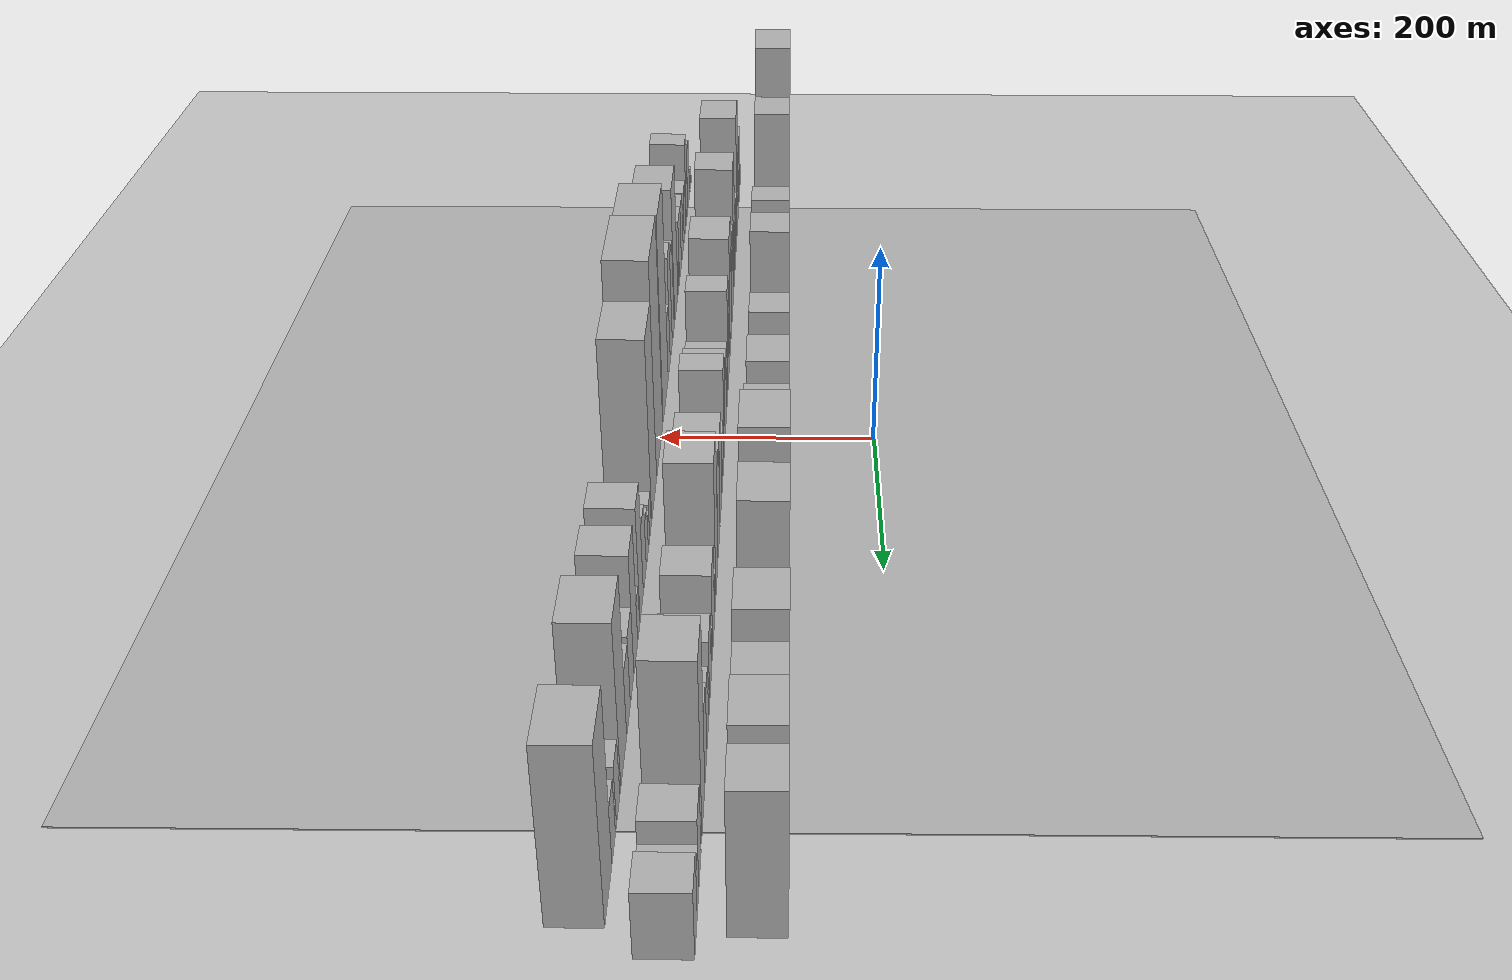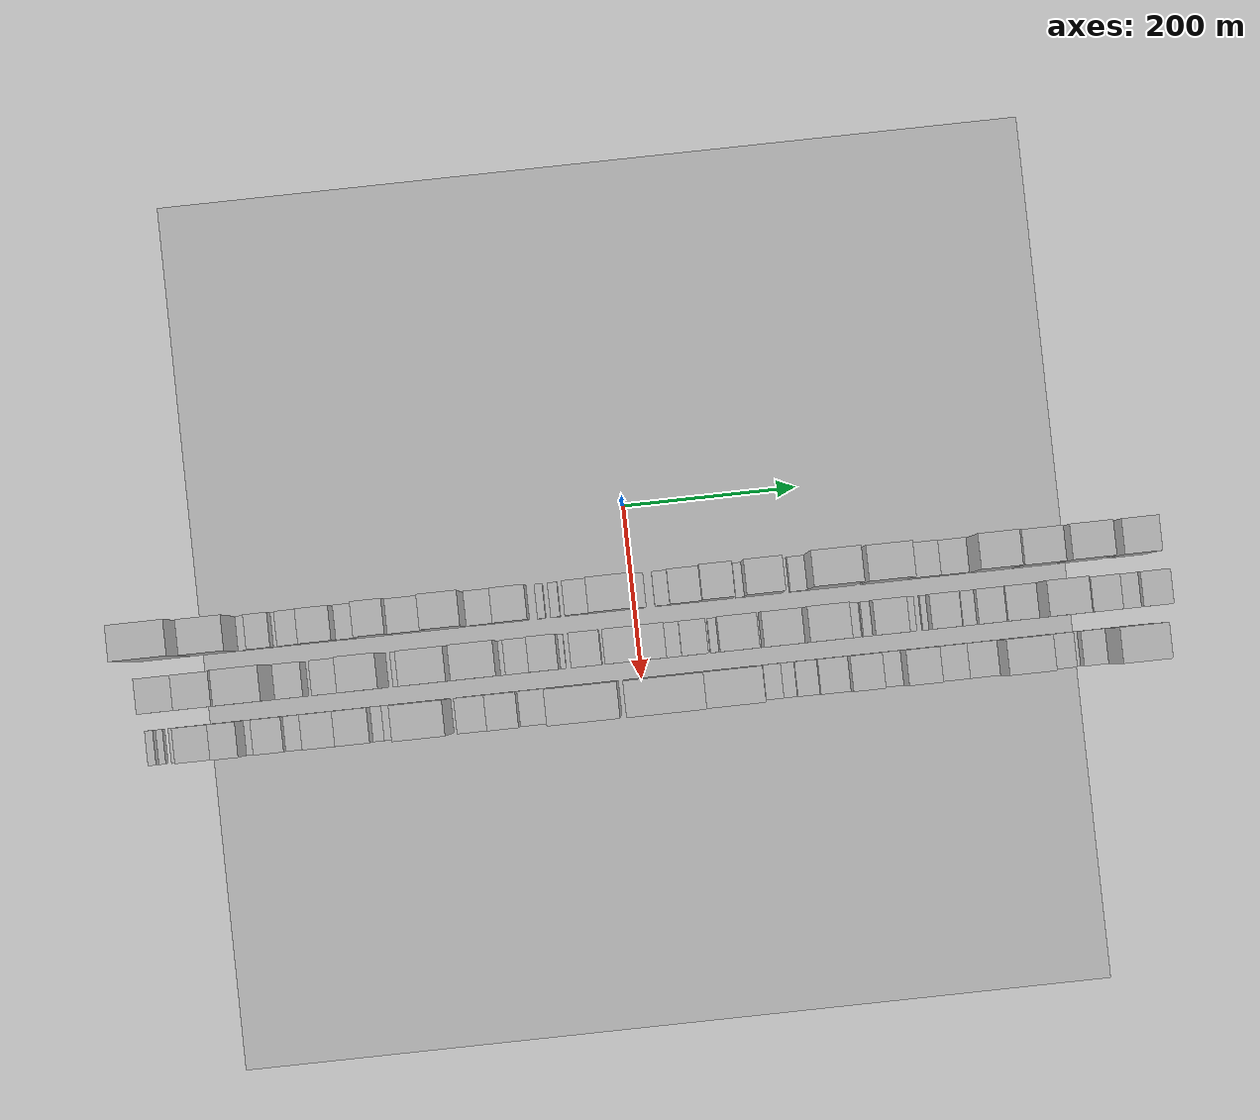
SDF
<?xml version="1.0" encoding="utf-8"?>

<sdf version="1.6">

   <world name="default">

      <gui fullscreen="0">

         <camera name="user_camera">

            <pose>-15 0 4.57585 0 0 0</pose>

            <view_controller>orbit</view_controller>

         </camera>

      </gui>

      <scene>

         <sky>

           <clouds>

             <speed>12</speed>

           </clouds>

         </sky>

         <ambient>0.4 0.4 0.4 1</ambient>

         <background>0.7 0.7 0.7 1</background>

         <shadows>1</shadows>

      </scene>

      <gravity>0 0 -9.8066</gravity>

      <magnetic_field>6e-06 2.3e-05 -4.2e-05</magnetic_field>

      <physics default="0" name="default_physics" type="ode">

         <ode>

            <solver>

               <type>quick</type>

               <iters>10</iters>

               <sor>1.0</sor>

               <use_dynamic_moi_rescaling>0</use_dynamic_moi_rescaling>

            </solver>

            <constraints>

               <cfm>0</cfm>

               <erp>0.2</erp>

               <contact_max_correcting_vel>100</contact_max_correcting_vel>

               <contact_surface_layer>0.001</contact_surface_layer>

            </constraints>

         </ode>

         <max_step_size>0.004</max_step_size>

         <real_time_factor>1</real_time_factor>

         <real_time_update_rate>250</real_time_update_rate>

      </physics>

      <light name="sun" type="directional">

         <cast_shadows>1</cast_shadows>

         <pose>0 0 10 0 0 0</pose>

         <diffuse>0.8 0.8 0.8 1</diffuse>

         <specular>0.2 0.2 0.2 1</specular>

         <attenuation>

            <range>1000</range>

            <constant>0.9</constant>

            <linear>0.01</linear>

            <quadratic>0.001</quadratic>

         </attenuation>

         <direction>-0.5 0.1 -0.9</direction>

      </light>

      <include>

         <name>ground_plane_1</name>

         <uri>model://HANNAS_ground_plane</uri>

         <pose>0 0 0  0 0 0</pose>

      </include>

      <include>

         <name>ground_plane_2</name>

         <uri>model://HANNAS_ground_plane</uri>

         <pose>100 0 0  0 0 0</pose>

      </include>

      <model name="building_1">

         <static>1</static>

         <pose frame="">100.0000 -543.1058 0 0.000000 0.000000 0.000000</pose>

         <link name="link">

            <pose frame="">0 0 97.50 0 0 0</pose>

            <collision name="collision">

               <geometry>

                  <box>

                     <size>40.0000 63.7884 195.0000</size>

                  </box>

               </geometry>

               <max_contacts>10</max_contacts>

               <surface>

                  <contact>

                     <ode/>

                  </contact>

                  <bounce/>

                  <friction>

                     <torsional>

                        <ode/>

                     </torsional>

                     <ode/>

                  </friction>

               </surface>

            </collision>

            <visual name="visual">

               <cast_shadows>0</cast_shadows>

               <geometry>

                  <box>

                     <size>40.0000 63.7884 195.0000</size>

                  </box>

               </geometry>

               <material>

                  <script>

                     <uri>model://HANNAS_wall/materials/scripts</uri>

                     <uri>model://HANNAS_wall/materials/textures</uri>

                     <name>vrc/HANNAS_wall</name>

                  </script>

               </material>

            </visual>

            <self_collide>0</self_collide>

            <enable_wind>0</enable_wind>

            <kinematic>0</kinematic>

         </link>

      </model>

      <model name="building_2">

         <static>1</static>

         <pose frame="">100.0000 -481.8896 0 0.000000 0.000000 0.000000</pose>

         <link name="link">

            <pose frame="">0 0 69.00 0 0 0</pose>

            <collision name="collision">

               <geometry>

                  <box>

                     <size>40.0000 50.6441 138.0000</size>

                  </box>

               </geometry>

               <max_contacts>10</max_contacts>

               <surface>

                  <contact>

                     <ode/>

                  </contact>

                  <bounce/>

                  <friction>

                     <torsional>

                        <ode/>

                     </torsional>

                     <ode/>

                  </friction>

               </surface>

            </collision>

            <visual name="visual">

               <cast_shadows>0</cast_shadows>

               <geometry>

                  <box>

                     <size>40.0000 50.6441 138.0000</size>

                  </box>

               </geometry>

               <material>

                  <script>

                     <uri>model://HANNAS_wall/materials/scripts</uri>

                     <uri>model://HANNAS_wall/materials/textures</uri>

                     <name>vrc/HANNAS_wall</name>

                  </script>

               </material>

            </visual>

            <self_collide>0</self_collide>

            <enable_wind>0</enable_wind>

            <kinematic>0</kinematic>

         </link>

      </model>

      <model name="building_3">

         <static>1</static>

         <pose frame="">100.0000 -451.5362 0 0.000000 0.000000 0.000000</pose>

         <link name="link">

            <pose frame="">0 0 10.50 0 0 0</pose>

            <collision name="collision">

               <geometry>

                  <box>

                     <size>40.0000 10.0627 21.0000</size>

                  </box>

               </geometry>

               <max_contacts>10</max_contacts>

               <surface>

                  <contact>

                     <ode/>

                  </contact>

                  <bounce/>

                  <friction>

                     <torsional>

                        <ode/>

                     </torsional>

                     <ode/>

                  </friction>

               </surface>

            </collision>

            <visual name="visual">

               <cast_shadows>0</cast_shadows>

               <geometry>

                  <box>

                     <size>40.0000 10.0627 21.0000</size>

                  </box>

               </geometry>

               <material>

                  <script>

                     <uri>model://HANNAS_wall/materials/scripts</uri>

                     <uri>model://HANNAS_wall/materials/textures</uri>

                     <name>vrc/HANNAS_wall</name>

                  </script>

               </material>

            </visual>

            <self_collide>0</self_collide>

            <enable_wind>0</enable_wind>

            <kinematic>0</kinematic>

         </link>

      </model>

      <model name="building_4">

         <static>1</static>

         <pose frame="">100.0000 -429.8259 0 0.000000 0.000000 0.000000</pose>

         <link name="link">

            <pose frame="">0 0 25.50 0 0 0</pose>

            <collision name="collision">

               <geometry>

                  <box>

                     <size>40.0000 27.3578 51.0000</size>

                  </box>

               </geometry>

               <max_contacts>10</max_contacts>

               <surface>

                  <contact>

                     <ode/>

                  </contact>

                  <bounce/>

                  <friction>

                     <torsional>

                        <ode/>

                     </torsional>

                     <ode/>

                  </friction>

               </surface>

            </collision>

            <visual name="visual">

               <cast_shadows>0</cast_shadows>

               <geometry>

                  <box>

                     <size>40.0000 27.3578 51.0000</size>

                  </box>

               </geometry>

               <material>

                  <script>

                     <uri>model://HANNAS_wall/materials/scripts</uri>

                     <uri>model://HANNAS_wall/materials/textures</uri>

                     <name>vrc/HANNAS_wall</name>

                  </script>

               </material>

            </visual>

            <self_collide>0</self_collide>

            <enable_wind>0</enable_wind>

            <kinematic>0</kinematic>

         </link>

      </model>

      <model name="building_5">

         <static>1</static>

         <pose frame="">100.0000 -412.1464 0 0.000000 0.000000 0.000000</pose>

         <link name="link">

            <pose frame="">0 0 9.00 0 0 0</pose>

            <collision name="collision">

               <geometry>

                  <box>

                     <size>40.0000 8.0012 18.0000</size>

                  </box>

               </geometry>

               <max_contacts>10</max_contacts>

               <surface>

                  <contact>

                     <ode/>

                  </contact>

                  <bounce/>

                  <friction>

                     <torsional>

                        <ode/>

                     </torsional>

                     <ode/>

                  </friction>

               </surface>

            </collision>

            <visual name="visual">

               <cast_shadows>0</cast_shadows>

               <geometry>

                  <box>

                     <size>40.0000 8.0012 18.0000</size>

                  </box>

               </geometry>

               <material>

                  <script>

                     <uri>model://HANNAS_wall/materials/scripts</uri>

                     <uri>model://HANNAS_wall/materials/textures</uri>

                     <name>vrc/HANNAS_wall</name>

                  </script>

               </material>

            </visual>

            <self_collide>0</self_collide>

            <enable_wind>0</enable_wind>

            <kinematic>0</kinematic>

         </link>

      </model>

      <model name="building_6">

         <static>1</static>

         <pose frame="">100.0000 -395.3940 0 0.000000 0.000000 0.000000</pose>

         <link name="link">

            <pose frame="">0 0 25.50 0 0 0</pose>

            <collision name="collision">

               <geometry>

                  <box>

                     <size>40.0000 25.5038 51.0000</size>

                  </box>

               </geometry>

               <max_contacts>10</max_contacts>

               <surface>

                  <contact>

                     <ode/>

                  </contact>

                  <bounce/>

                  <friction>

                     <torsional>

                        <ode/>

                     </torsional>

                     <ode/>

                  </friction>

               </surface>

            </collision>

            <visual name="visual">

               <cast_shadows>0</cast_shadows>

               <geometry>

                  <box>

                     <size>40.0000 25.5038 51.0000</size>

                  </box>

               </geometry>

               <material>

                  <script>

                     <uri>model://HANNAS_wall/materials/scripts</uri>

                     <uri>model://HANNAS_wall/materials/textures</uri>

                     <name>vrc/HANNAS_wall</name>

                  </script>

               </material>

            </visual>

            <self_collide>0</self_collide>

            <enable_wind>0</enable_wind>

            <kinematic>0</kinematic>

         </link>

      </model>

      <model name="building_7">

         <static>1</static>

         <pose frame="">100.0000 -363.7323 0 0.000000 0.000000 0.000000</pose>

         <link name="link">

            <pose frame="">0 0 33.00 0 0 0</pose>

            <collision name="collision">

               <geometry>

                  <box>

                     <size>40.0000 37.8195 66.0000</size>

                  </box>

               </geometry>

               <max_contacts>10</max_contacts>

               <surface>

                  <contact>

                     <ode/>

                  </contact>

                  <bounce/>

                  <friction>

                     <torsional>

                        <ode/>

                     </torsional>

                     <ode/>

                  </friction>

               </surface>

            </collision>

            <visual name="visual">

               <cast_shadows>0</cast_shadows>

               <geometry>

                  <box>

                     <size>40.0000 37.8195 66.0000</size>

                  </box>

               </geometry>

               <material>

                  <script>

                     <uri>model://HANNAS_wall/materials/scripts</uri>

                     <uri>model://HANNAS_wall/materials/textures</uri>

                     <name>vrc/HANNAS_wall</name>

                  </script>

               </material>

            </visual>

            <self_collide>0</self_collide>

            <enable_wind>0</enable_wind>

            <kinematic>0</kinematic>

         </link>

      </model>

      <model name="building_8">

         <static>1</static>

         <pose frame="">100.0000 -327.9624 0 0.000000 0.000000 0.000000</pose>

         <link name="link">

            <pose frame="">0 0 25.50 0 0 0</pose>

            <collision name="collision">

               <geometry>

                  <box>

                     <size>40.0000 25.7202 51.0000</size>

                  </box>

               </geometry>

               <max_contacts>10</max_contacts>

               <surface>

                  <contact>

                     <ode/>

                  </contact>

                  <bounce/>

                  <friction>

                     <torsional>

                        <ode/>

                     </torsional>

                     <ode/>

                  </friction>

               </surface>

            </collision>

            <visual name="visual">

               <cast_shadows>0</cast_shadows>

               <geometry>

                  <box>

                     <size>40.0000 25.7202 51.0000</size>

                  </box>

               </geometry>

               <material>

                  <script>

                     <uri>model://HANNAS_wall/materials/scripts</uri>

                     <uri>model://HANNAS_wall/materials/textures</uri>

                     <name>vrc/HANNAS_wall</name>

                  </script>

               </material>

            </visual>

            <self_collide>0</self_collide>

            <enable_wind>0</enable_wind>

            <kinematic>0</kinematic>

         </link>

      </model>

      <model name="building_9">

         <static>1</static>

         <pose frame="">100.0000 -297.5319 0 0.000000 0.000000 0.000000</pose>

         <link name="link">

            <pose frame="">0 0 57.00 0 0 0</pose>

            <collision name="collision">

               <geometry>

                  <box>

                     <size>40.0000 35.1408 114.0000</size>

                  </box>

               </geometry>

               <max_contacts>10</max_contacts>

               <surface>

                  <contact>

                     <ode/>

                  </contact>

                  <bounce/>

                  <friction>

                     <torsional>

                        <ode/>

                     </torsional>

                     <ode/>

                  </friction>

               </surface>

            </collision>

            <visual name="visual">

               <cast_shadows>0</cast_shadows>

               <geometry>

                  <box>

                     <size>40.0000 35.1408 114.0000</size>

                  </box>

               </geometry>

               <material>

                  <script>

                     <uri>model://HANNAS_wall/materials/scripts</uri>

                     <uri>model://HANNAS_wall/materials/textures</uri>

                     <name>vrc/HANNAS_wall</name>

                  </script>

               </material>

            </visual>

            <self_collide>0</self_collide>

            <enable_wind>0</enable_wind>

            <kinematic>0</kinematic>

         </link>

      </model>

      <model name="building_10">

         <static>1</static>

         <pose frame="">100.0000 -260.0254 0 0.000000 0.000000 0.000000</pose>

         <link name="link">

            <pose frame="">0 0 37.50 0 0 0</pose>

            <collision name="collision">

               <geometry>

                  <box>

                     <size>40.0000 39.8721 75.0000</size>

                  </box>

               </geometry>

               <max_contacts>10</max_contacts>

               <surface>

                  <contact>

                     <ode/>

                  </contact>

                  <bounce/>

                  <friction>

                     <torsional>

                        <ode/>

                     </torsional>

                     <ode/>

                  </friction>

               </surface>

            </collision>

            <visual name="visual">

               <cast_shadows>0</cast_shadows>

               <geometry>

                  <box>

                     <size>40.0000 39.8721 75.0000</size>

                  </box>

               </geometry>

               <material>

                  <script>

                     <uri>model://HANNAS_wall/materials/scripts</uri>

                     <uri>model://HANNAS_wall/materials/textures</uri>

                     <name>vrc/HANNAS_wall</name>

                  </script>

               </material>

            </visual>

            <self_collide>0</self_collide>

            <enable_wind>0</enable_wind>

            <kinematic>0</kinematic>

         </link>

      </model>

      <model name="building_11">

         <static>1</static>

         <pose frame="">100.0000 -217.4439 0 0.000000 0.000000 0.000000</pose>

         <link name="link">

            <pose frame="">0 0 60.00 0 0 0</pose>

            <collision name="collision">

               <geometry>

                  <box>

                     <size>40.0000 45.2909 120.0000</size>

                  </box>

               </geometry>

               <max_contacts>10</max_contacts>

               <surface>

                  <contact>

                     <ode/>

                  </contact>

                  <bounce/>

                  <friction>

                     <torsional>

                        <ode/>

                     </torsional>

                     <ode/>

                  </friction>

               </surface>

            </collision>

            <visual name="visual">

               <cast_shadows>0</cast_shadows>

               <geometry>

                  <box>

                     <size>40.0000 45.2909 120.0000</size>

                  </box>

               </geometry>

               <material>

                  <script>

                     <uri>model://HANNAS_wall/materials/scripts</uri>

                     <uri>model://HANNAS_wall/materials/textures</uri>

                     <name>vrc/HANNAS_wall</name>

                  </script>

               </material>

            </visual>

            <self_collide>0</self_collide>

            <enable_wind>0</enable_wind>

            <kinematic>0</kinematic>

         </link>

      </model>

      <model name="building_12">

         <static>1</static>

         <pose frame="">100.0000 -176.5121 0 0.000000 0.000000 0.000000</pose>

         <link name="link">

            <pose frame="">0 0 25.50 0 0 0</pose>

            <collision name="collision">

               <geometry>

                  <box>

                     <size>40.0000 30.5726 51.0000</size>

                  </box>

               </geometry>

               <max_contacts>10</max_contacts>

               <surface>

                  <contact>

                     <ode/>

                  </contact>

                  <bounce/>

                  <friction>

                     <torsional>

                        <ode/>

                     </torsional>

                     <ode/>

                  </friction>

               </surface>

            </collision>

            <visual name="visual">

               <cast_shadows>0</cast_shadows>

               <geometry>

                  <box>

                     <size>40.0000 30.5726 51.0000</size>

                  </box>

               </geometry>

               <material>

                  <script>

                     <uri>model://HANNAS_wall/materials/scripts</uri>

                     <uri>model://HANNAS_wall/materials/textures</uri>

                     <name>vrc/HANNAS_wall</name>

                  </script>

               </material>

            </visual>

            <self_collide>0</self_collide>

            <enable_wind>0</enable_wind>

            <kinematic>0</kinematic>

         </link>

      </model>

      <model name="building_13">

         <static>1</static>

         <pose frame="">100.0000 -141.3130 0 0.000000 0.000000 0.000000</pose>

         <link name="link">

            <pose frame="">0 0 34.50 0 0 0</pose>

            <collision name="collision">

               <geometry>

                  <box>

                     <size>40.0000 39.8254 69.0000</size>

                  </box>

               </geometry>

               <max_contacts>10</max_contacts>

               <surface>

                  <contact>

                     <ode/>

                  </contact>

                  <bounce/>

                  <friction>

                     <torsional>

                        <ode/>

                     </torsional>

                     <ode/>

                  </friction>

               </surface>

            </collision>

            <visual name="visual">

               <cast_shadows>0</cast_shadows>

               <geometry>

                  <box>

                     <size>40.0000 39.8254 69.0000</size>

                  </box>

               </geometry>

               <material>

                  <script>

                     <uri>model://HANNAS_wall/materials/scripts</uri>

                     <uri>model://HANNAS_wall/materials/textures</uri>

                     <name>vrc/HANNAS_wall</name>

                  </script>

               </material>

            </visual>

            <self_collide>0</self_collide>

            <enable_wind>0</enable_wind>

            <kinematic>0</kinematic>

         </link>

      </model>

      <model name="building_14">

         <static>1</static>

         <pose frame="">100.0000 -106.7540 0 0.000000 0.000000 0.000000</pose>

         <link name="link">

            <pose frame="">0 0 10.50 0 0 0</pose>

            <collision name="collision">

               <geometry>

                  <box>

                     <size>40.0000 9.2926 21.0000</size>

                  </box>

               </geometry>

               <max_contacts>10</max_contacts>

               <surface>

                  <contact>

                     <ode/>

                  </contact>

                  <bounce/>

                  <friction>

                     <torsional>

                        <ode/>

                     </torsional>

                     <ode/>

                  </friction>

               </surface>

            </collision>

            <visual name="visual">

               <cast_shadows>0</cast_shadows>

               <geometry>

                  <box>

                     <size>40.0000 9.2926 21.0000</size>

                  </box>

               </geometry>

               <material>

                  <script>

                     <uri>model://HANNAS_wall/materials/scripts</uri>

                     <uri>model://HANNAS_wall/materials/textures</uri>

                     <name>vrc/HANNAS_wall</name>

                  </script>

               </material>

            </visual>

            <self_collide>0</self_collide>

            <enable_wind>0</enable_wind>

            <kinematic>0</kinematic>

         </link>

      </model>

      <model name="building_15">

         <static>1</static>

         <pose frame="">100.0000 -90.6586 0 0.000000 0.000000 0.000000</pose>

         <link name="link">

            <pose frame="">0 0 12.00 0 0 0</pose>

            <collision name="collision">

               <geometry>

                  <box>

                     <size>40.0000 10.8982 24.0000</size>

                  </box>

               </geometry>

               <max_contacts>10</max_contacts>

               <surface>

                  <contact>

                     <ode/>

                  </contact>

                  <bounce/>

                  <friction>

                     <torsional>

                        <ode/>

                     </torsional>

                     <ode/>

                  </friction>

               </surface>

            </collision>

            <visual name="visual">

               <cast_shadows>0</cast_shadows>

               <geometry>

                  <box>

                     <size>40.0000 10.8982 24.0000</size>

                  </box>

               </geometry>

               <material>

                  <script>

                     <uri>model://HANNAS_wall/materials/scripts</uri>

                     <uri>model://HANNAS_wall/materials/textures</uri>

                     <name>vrc/HANNAS_wall</name>

                  </script>

               </material>

            </visual>

            <self_collide>0</self_collide>

            <enable_wind>0</enable_wind>

            <kinematic>0</kinematic>

         </link>

      </model>

      <model name="building_16">

         <static>1</static>

         <pose frame="">100.0000 -65.3820 0 0.000000 0.000000 0.000000</pose>

         <link name="link">

            <pose frame="">0 0 25.50 0 0 0</pose>

            <collision name="collision">

               <geometry>

                  <box>

                     <size>40.0000 27.6551 51.0000</size>

                  </box>

               </geometry>

               <max_contacts>10</max_contacts>

               <surface>

                  <contact>

                     <ode/>

                  </contact>

                  <bounce/>

                  <friction>

                     <torsional>

                        <ode/>

                     </torsional>

                     <ode/>

                  </friction>

               </surface>

            </collision>

            <visual name="visual">

               <cast_shadows>0</cast_shadows>

               <geometry>

                  <box>

                     <size>40.0000 27.6551 51.0000</size>

                  </box>

               </geometry>

               <material>

                  <script>

                     <uri>model://HANNAS_wall/materials/scripts</uri>

                     <uri>model://HANNAS_wall/materials/textures</uri>

                     <name>vrc/HANNAS_wall</name>

                  </script>

               </material>

            </visual>

            <self_collide>0</self_collide>

            <enable_wind>0</enable_wind>

            <kinematic>0</kinematic>

         </link>

      </model>

      <model name="building_17">

         <static>1</static>

         <pose frame="">100.0000 -26.5181 0 0.000000 0.000000 0.000000</pose>

         <link name="link">

            <pose frame="">0 0 42.00 0 0 0</pose>

            <collision name="collision">

               <geometry>

                  <box>

                     <size>40.0000 50.0727 84.0000</size>

                  </box>

               </geometry>

               <max_contacts>10</max_contacts>

               <surface>

                  <contact>

                     <ode/>

                  </contact>

                  <bounce/>

                  <friction>

                     <torsional>

                        <ode/>

                     </torsional>

                     <ode/>

                  </friction>

               </surface>

            </collision>

            <visual name="visual">

               <cast_shadows>0</cast_shadows>

               <geometry>

                  <box>

                     <size>40.0000 50.0727 84.0000</size>

                  </box>

               </geometry>

               <material>

                  <script>

                     <uri>model://HANNAS_wall/materials/scripts</uri>

                     <uri>model://HANNAS_wall/materials/textures</uri>

                     <name>vrc/HANNAS_wall</name>

                  </script>

               </material>

            </visual>

            <self_collide>0</self_collide>

            <enable_wind>0</enable_wind>

            <kinematic>0</kinematic>

         </link>

      </model>

      <model name="building_18">

         <static>1</static>

         <pose frame="">100.0000 6.2643 0 0.000000 0.000000 0.000000</pose>

         <link name="link">

            <pose frame="">0 0 15.00 0 0 0</pose>

            <collision name="collision">

               <geometry>

                  <box>

                     <size>40.0000 15.4921 30.0000</size>

                  </box>

               </geometry>

               <max_contacts>10</max_contacts>

               <surface>

                  <contact>

                     <ode/>

                  </contact>

                  <bounce/>

                  <friction>

                     <torsional>

                        <ode/>

                     </torsional>

                     <ode/>

                  </friction>

               </surface>

            </collision>

            <visual name="visual">

               <cast_shadows>0</cast_shadows>

               <geometry>

                  <box>

                     <size>40.0000 15.4921 30.0000</size>

                  </box>

               </geometry>

               <material>

                  <script>

                     <uri>model://HANNAS_wall/materials/scripts</uri>

                     <uri>model://HANNAS_wall/materials/textures</uri>

                     <name>vrc/HANNAS_wall</name>

                  </script>

               </material>

            </visual>

            <self_collide>0</self_collide>

            <enable_wind>0</enable_wind>

            <kinematic>0</kinematic>

         </link>

      </model>

      <model name="building_19">

         <static>1</static>

         <pose frame="">100.0000 32.5690 0 0.000000 0.000000 0.000000</pose>

         <link name="link">

            <pose frame="">0 0 16.50 0 0 0</pose>

            <collision name="collision">

               <geometry>

                  <box>

                     <size>40.0000 17.1172 33.0000</size>

                  </box>

               </geometry>

               <max_contacts>10</max_contacts>

               <surface>

                  <contact>

                     <ode/>

                  </contact>

                  <bounce/>

                  <friction>

                     <torsional>

                        <ode/>

                     </torsional>

                     <ode/>

                  </friction>

               </surface>

            </collision>

            <visual name="visual">

               <cast_shadows>0</cast_shadows>

               <geometry>

                  <box>

                     <size>40.0000 17.1172 33.0000</size>

                  </box>

               </geometry>

               <material>

                  <script>

                     <uri>model://HANNAS_wall/materials/scripts</uri>

                     <uri>model://HANNAS_wall/materials/textures</uri>

                     <name>vrc/HANNAS_wall</name>

                  </script>

               </material>

            </visual>

            <self_collide>0</self_collide>

            <enable_wind>0</enable_wind>

            <kinematic>0</kinematic>

         </link>

      </model>

      <model name="building_20">

         <static>1</static>

         <pose frame="">100.0000 59.2023 0 0.000000 0.000000 0.000000</pose>

         <link name="link">

            <pose frame="">0 0 31.50 0 0 0</pose>

            <collision name="collision">

               <geometry>

                  <box>

                     <size>40.0000 36.1495 63.0000</size>

                  </box>

               </geometry>

               <max_contacts>10</max_contacts>

               <surface>

                  <contact>

                     <ode/>

                  </contact>

                  <bounce/>

                  <friction>

                     <torsional>

                        <ode/>

                     </torsional>

                     <ode/>

                  </friction>

               </surface>

            </collision>

            <visual name="visual">

               <cast_shadows>0</cast_shadows>

               <geometry>

                  <box>

                     <size>40.0000 36.1495 63.0000</size>

                  </box>

               </geometry>

               <material>

                  <script>

                     <uri>model://HANNAS_wall/materials/scripts</uri>

                     <uri>model://HANNAS_wall/materials/textures</uri>

                     <name>vrc/HANNAS_wall</name>

                  </script>

               </material>

            </visual>

            <self_collide>0</self_collide>

            <enable_wind>0</enable_wind>

            <kinematic>0</kinematic>

         </link>

      </model>

      <model name="building_21">

         <static>1</static>

         <pose frame="">100.0000 95.7717 0 0.000000 0.000000 0.000000</pose>

         <link name="link">

            <pose frame="">0 0 54.00 0 0 0</pose>

            <collision name="collision">

               <geometry>

                  <box>

                     <size>40.0000 36.9893 108.0000</size>

                  </box>

               </geometry>

               <max_contacts>10</max_contacts>

               <surface>

                  <contact>

                     <ode/>

                  </contact>

                  <bounce/>

                  <friction>

                     <torsional>

                        <ode/>

                     </torsional>

                     <ode/>

                  </friction>

               </surface>

            </collision>

            <visual name="visual">

               <cast_shadows>0</cast_shadows>

               <geometry>

                  <box>

                     <size>40.0000 36.9893 108.0000</size>

                  </box>

               </geometry>

               <material>

                  <script>

                     <uri>model://HANNAS_wall/materials/scripts</uri>

                     <uri>model://HANNAS_wall/materials/textures</uri>

                     <name>vrc/HANNAS_wall</name>

                  </script>

               </material>

            </visual>

            <self_collide>0</self_collide>

            <enable_wind>0</enable_wind>

            <kinematic>0</kinematic>

         </link>

      </model>

      <model name="building_22">

         <static>1</static>

         <pose frame="">100.0000 122.1732 0 0.000000 0.000000 0.000000</pose>

         <link name="link">

            <pose frame="">0 0 12.00 0 0 0</pose>

            <collision name="collision">

               <geometry>

                  <box>

                     <size>40.0000 9.8138 24.0000</size>

                  </box>

               </geometry>

               <max_contacts>10</max_contacts>

               <surface>

                  <contact>

                     <ode/>

                  </contact>

                  <bounce/>

                  <friction>

                     <torsional>

                        <ode/>

                     </torsional>

                     <ode/>

                  </friction>

               </surface>

            </collision>

            <visual name="visual">

               <cast_shadows>0</cast_shadows>

               <geometry>

                  <box>

                     <size>40.0000 9.8138 24.0000</size>

                  </box>

               </geometry>

               <material>

                  <script>

                     <uri>model://HANNAS_wall/materials/scripts</uri>

                     <uri>model://HANNAS_wall/materials/textures</uri>

                     <name>vrc/HANNAS_wall</name>

                  </script>

               </material>

            </visual>

            <self_collide>0</self_collide>

            <enable_wind>0</enable_wind>

            <kinematic>0</kinematic>

         </link>

      </model>

      <model name="building_23">

         <static>1</static>

         <pose frame="">100.0000 148.9118 0 0.000000 0.000000 0.000000</pose>

         <link name="link">

            <pose frame="">0 0 60.00 0 0 0</pose>

            <collision name="collision">

               <geometry>

                  <box>

                     <size>40.0000 43.6633 120.0000</size>

                  </box>

               </geometry>

               <max_contacts>10</max_contacts>

               <surface>

                  <contact>

                     <ode/>

                  </contact>

                  <bounce/>

                  <friction>

                     <torsional>

                        <ode/>

                     </torsional>

                     <ode/>

                  </friction>

               </surface>

            </collision>

            <visual name="visual">

               <cast_shadows>0</cast_shadows>

               <geometry>

                  <box>

                     <size>40.0000 43.6633 120.0000</size>

                  </box>

               </geometry>

               <material>

                  <script>

                     <uri>model://HANNAS_wall/materials/scripts</uri>

                     <uri>model://HANNAS_wall/materials/textures</uri>

                     <name>vrc/HANNAS_wall</name>

                  </script>

               </material>

            </visual>

            <self_collide>0</self_collide>

            <enable_wind>0</enable_wind>

            <kinematic>0</kinematic>

         </link>

      </model>

      <model name="building_24">

         <static>1</static>

         <pose frame="">100.0000 189.5372 0 0.000000 0.000000 0.000000</pose>

         <link name="link">

            <pose frame="">0 0 16.50 0 0 0</pose>

            <collision name="collision">

               <geometry>

                  <box>

                     <size>40.0000 19.5876 33.0000</size>

                  </box>

               </geometry>

               <max_contacts>10</max_contacts>

               <surface>

                  <contact>

                     <ode/>

                  </contact>

                  <bounce/>

                  <friction>

                     <torsional>

                        <ode/>

                     </torsional>

                     <ode/>

                  </friction>

               </surface>

            </collision>

            <visual name="visual">

               <cast_shadows>0</cast_shadows>

               <geometry>

                  <box>

                     <size>40.0000 19.5876 33.0000</size>

                  </box>

               </geometry>

               <material>

                  <script>

                     <uri>model://HANNAS_wall/materials/scripts</uri>

                     <uri>model://HANNAS_wall/materials/textures</uri>

                     <name>vrc/HANNAS_wall</name>

                  </script>

               </material>

            </visual>

            <self_collide>0</self_collide>

            <enable_wind>0</enable_wind>

            <kinematic>0</kinematic>

         </link>

      </model>

      <model name="building_25">

         <static>1</static>

         <pose frame="">100.0000 227.2445 0 0.000000 0.000000 0.000000</pose>

         <link name="link">

            <pose frame="">0 0 88.50 0 0 0</pose>

            <collision name="collision">

               <geometry>

                  <box>

                     <size>40.0000 55.8271 177.0000</size>

                  </box>

               </geometry>

               <max_contacts>10</max_contacts>

               <surface>

                  <contact>

                     <ode/>

                  </contact>

                  <bounce/>

                  <friction>

                     <torsional>

                        <ode/>

                     </torsional>

                     <ode/>

                  </friction>

               </surface>

            </collision>

            <visual name="visual">

               <cast_shadows>0</cast_shadows>

               <geometry>

                  <box>

                     <size>40.0000 55.8271 177.0000</size>

                  </box>

               </geometry>

               <material>

                  <script>

                     <uri>model://HANNAS_wall/materials/scripts</uri>

                     <uri>model://HANNAS_wall/materials/textures</uri>

                     <name>vrc/HANNAS_wall</name>

                  </script>

               </material>

            </visual>

            <self_collide>0</self_collide>

            <enable_wind>0</enable_wind>

            <kinematic>0</kinematic>

         </link>

      </model>

      <model name="building_26">

         <static>1</static>

         <pose frame="">100.0000 288.1482 0 0.000000 0.000000 0.000000</pose>

         <link name="link">

            <pose frame="">0 0 75.00 0 0 0</pose>

            <collision name="collision">

               <geometry>

                  <box>

                     <size>40.0000 51.9804 150.0000</size>

                  </box>

               </geometry>

               <max_contacts>10</max_contacts>

               <surface>

                  <contact>

                     <ode/>

                  </contact>

                  <bounce/>

                  <friction>

                     <torsional>

                        <ode/>

                     </torsional>

                     <ode/>

                  </friction>

               </surface>

            </collision>

            <visual name="visual">

               <cast_shadows>0</cast_shadows>

               <geometry>

                  <box>

                     <size>40.0000 51.9804 150.0000</size>

                  </box>

               </geometry>

               <material>

                  <script>

                     <uri>model://HANNAS_wall/materials/scripts</uri>

                     <uri>model://HANNAS_wall/materials/textures</uri>

                     <name>vrc/HANNAS_wall</name>

                  </script>

               </material>

            </visual>

            <self_collide>0</self_collide>

            <enable_wind>0</enable_wind>

            <kinematic>0</kinematic>

         </link>

      </model>

      <model name="building_27">

         <static>1</static>

         <pose frame="">100.0000 331.9754 0 0.000000 0.000000 0.000000</pose>

         <link name="link">

            <pose frame="">0 0 34.50 0 0 0</pose>

            <collision name="collision">

               <geometry>

                  <box>

                     <size>40.0000 35.6739 69.0000</size>

                  </box>

               </geometry>

               <max_contacts>10</max_contacts>

               <surface>

                  <contact>

                     <ode/>

                  </contact>

                  <bounce/>

                  <friction>

                     <torsional>

                        <ode/>

                     </torsional>

                     <ode/>

                  </friction>

               </surface>

            </collision>

            <visual name="visual">

               <cast_shadows>0</cast_shadows>

               <geometry>

                  <box>

                     <size>40.0000 35.6739 69.0000</size>

                  </box>

               </geometry>

               <material>

                  <script>

                     <uri>model://HANNAS_wall/materials/scripts</uri>

                     <uri>model://HANNAS_wall/materials/textures</uri>

                     <name>vrc/HANNAS_wall</name>

                  </script>

               </material>

            </visual>

            <self_collide>0</self_collide>

            <enable_wind>0</enable_wind>

            <kinematic>0</kinematic>

         </link>

      </model>

      <model name="building_28">

         <static>1</static>

         <pose frame="">100.0000 366.4845 0 0.000000 0.000000 0.000000</pose>

         <link name="link">

            <pose frame="">0 0 28.50 0 0 0</pose>

            <collision name="collision">

               <geometry>

                  <box>

                     <size>40.0000 33.3442 57.0000</size>

                  </box>

               </geometry>

               <max_contacts>10</max_contacts>

               <surface>

                  <contact>

                     <ode/>

                  </contact>

                  <bounce/>

                  <friction>

                     <torsional>

                        <ode/>

                     </torsional>

                     <ode/>

                  </friction>

               </surface>

            </collision>

            <visual name="visual">

               <cast_shadows>0</cast_shadows>

               <geometry>

                  <box>

                     <size>40.0000 33.3442 57.0000</size>

                  </box>

               </geometry>

               <material>

                  <script>

                     <uri>model://HANNAS_wall/materials/scripts</uri>

                     <uri>model://HANNAS_wall/materials/textures</uri>

                     <name>vrc/HANNAS_wall</name>

                  </script>

               </material>

            </visual>

            <self_collide>0</self_collide>

            <enable_wind>0</enable_wind>

            <kinematic>0</kinematic>

         </link>

      </model>

      <model name="building_29">

         <static>1</static>

         <pose frame="">100.0000 410.5144 0 0.000000 0.000000 0.000000</pose>

         <link name="link">

            <pose frame="">0 0 72.00 0 0 0</pose>

            <collision name="collision">

               <geometry>

                  <box>

                     <size>40.0000 46.7158 144.0000</size>

                  </box>

               </geometry>

               <max_contacts>10</max_contacts>

               <surface>

                  <contact>

                     <ode/>

                  </contact>

                  <bounce/>

                  <friction>

                     <torsional>

                        <ode/>

                     </torsional>

                     <ode/>

                  </friction>

               </surface>

            </collision>

            <visual name="visual">

               <cast_shadows>0</cast_shadows>

               <geometry>

                  <box>

                     <size>40.0000 46.7158 144.0000</size>

                  </box>

               </geometry>

               <material>

                  <script>

                     <uri>model://HANNAS_wall/materials/scripts</uri>

                     <uri>model://HANNAS_wall/materials/textures</uri>

                     <name>vrc/HANNAS_wall</name>

                  </script>

               </material>

            </visual>

            <self_collide>0</self_collide>

            <enable_wind>0</enable_wind>

            <kinematic>0</kinematic>

         </link>

      </model>

      <model name="building_30">

         <static>1</static>

         <pose frame="">100.0000 462.2945 0 0.000000 0.000000 0.000000</pose>

         <link name="link">

            <pose frame="">0 0 60.00 0 0 0</pose>

            <collision name="collision">

               <geometry>

                  <box>

                     <size>40.0000 46.8444 120.0000</size>

                  </box>

               </geometry>

               <max_contacts>10</max_contacts>

               <surface>

                  <contact>

                     <ode/>

                  </contact>

                  <bounce/>

                  <friction>

                     <torsional>

                        <ode/>

                     </torsional>

                     <ode/>

                  </friction>

               </surface>

            </collision>

            <visual name="visual">

               <cast_shadows>0</cast_shadows>

               <geometry>

                  <box>

                     <size>40.0000 46.8444 120.0000</size>

                  </box>

               </geometry>

               <material>

                  <script>

                     <uri>model://HANNAS_wall/materials/scripts</uri>

                     <uri>model://HANNAS_wall/materials/textures</uri>

                     <name>vrc/HANNAS_wall</name>

                  </script>

               </material>

            </visual>

            <self_collide>0</self_collide>

            <enable_wind>0</enable_wind>

            <kinematic>0</kinematic>

         </link>

      </model>

      <model name="building_31">

         <static>1</static>

         <pose frame="">100.0000 515.0531 0 0.000000 0.000000 0.000000</pose>

         <link name="link">

            <pose frame="">0 0 67.50 0 0 0</pose>

            <collision name="collision">

               <geometry>

                  <box>

                     <size>40.0000 48.6727 135.0000</size>

                  </box>

               </geometry>

               <max_contacts>10</max_contacts>

               <surface>

                  <contact>

                     <ode/>

                  </contact>

                  <bounce/>

                  <friction>

                     <torsional>

                        <ode/>

                     </torsional>

                     <ode/>

                  </friction>

               </surface>

            </collision>

            <visual name="visual">

               <cast_shadows>0</cast_shadows>

               <geometry>

                  <box>

                     <size>40.0000 48.6727 135.0000</size>

                  </box>

               </geometry>

               <material>

                  <script>

                     <uri>model://HANNAS_wall/materials/scripts</uri>

                     <uri>model://HANNAS_wall/materials/textures</uri>

                     <name>vrc/HANNAS_wall</name>

                  </script>

               </material>

            </visual>

            <self_collide>0</self_collide>

            <enable_wind>0</enable_wind>

            <kinematic>0</kinematic>

         </link>

      </model>

      <model name="building_32">

         <static>1</static>

         <pose frame="">100.0000 570.4819 0 0.000000 0.000000 0.000000</pose>

         <link name="link">

            <pose frame="">0 0 64.50 0 0 0</pose>

            <collision name="collision">

               <geometry>

                  <box>

                     <size>40.0000 42.1849 129.0000</size>

                  </box>

               </geometry>

               <max_contacts>10</max_contacts>

               <surface>

                  <contact>

                     <ode/>

                  </contact>

                  <bounce/>

                  <friction>

                     <torsional>

                        <ode/>

                     </torsional>

                     <ode/>

                  </friction>

               </surface>

            </collision>

            <visual name="visual">

               <cast_shadows>0</cast_shadows>

               <geometry>

                  <box>

                     <size>40.0000 42.1849 129.0000</size>

                  </box>

               </geometry>

               <material>

                  <script>

                     <uri>model://HANNAS_wall/materials/scripts</uri>

                     <uri>model://HANNAS_wall/materials/textures</uri>

                     <name>vrc/HANNAS_wall</name>

                  </script>

               </material>

            </visual>

            <self_collide>0</self_collide>

            <enable_wind>0</enable_wind>

            <kinematic>0</kinematic>

         </link>

      </model>

      <model name="building_33">

         <static>1</static>

         <pose frame="">160.0000 -550.3264 0 0.000000 0.000000 0.000000</pose>

         <link name="link">

            <pose frame="">0 0 37.50 0 0 0</pose>

            <collision name="collision">

               <geometry>

                  <box>

                     <size>40.0000 41.3473 75.0000</size>

                  </box>

               </geometry>

               <max_contacts>10</max_contacts>

               <surface>

                  <contact>

                     <ode/>

                  </contact>

                  <bounce/>

                  <friction>

                     <torsional>

                        <ode/>

                     </torsional>

                     <ode/>

                  </friction>

               </surface>

            </collision>

            <visual name="visual">

               <cast_shadows>0</cast_shadows>

               <geometry>

                  <box>

                     <size>40.0000 41.3473 75.0000</size>

                  </box>

               </geometry>

               <material>

                  <script>

                     <uri>model://HANNAS_wall/materials/scripts</uri>

                     <uri>model://HANNAS_wall/materials/textures</uri>

                     <name>vrc/HANNAS_wall</name>

                  </script>

               </material>

            </visual>

            <self_collide>0</self_collide>

            <enable_wind>0</enable_wind>

            <kinematic>0</kinematic>

         </link>

      </model>

      <model name="building_34">

         <static>1</static>

         <pose frame="">160.0000 -508.0930 0 0.000000 0.000000 0.000000</pose>

         <link name="link">

            <pose frame="">0 0 37.50 0 0 0</pose>

            <collision name="collision">

               <geometry>

                  <box>

                     <size>40.0000 43.1194 75.0000</size>

                  </box>

               </geometry>

               <max_contacts>10</max_contacts>

               <surface>

                  <contact>

                     <ode/>

                  </contact>

                  <bounce/>

                  <friction>

                     <torsional>

                        <ode/>

                     </torsional>

                     <ode/>

                  </friction>

               </surface>

            </collision>

            <visual name="visual">

               <cast_shadows>0</cast_shadows>

               <geometry>

                  <box>

                     <size>40.0000 43.1194 75.0000</size>

                  </box>

               </geometry>

               <material>

                  <script>

                     <uri>model://HANNAS_wall/materials/scripts</uri>

                     <uri>model://HANNAS_wall/materials/textures</uri>

                     <name>vrc/HANNAS_wall</name>

                  </script>

               </material>

            </visual>

            <self_collide>0</self_collide>

            <enable_wind>0</enable_wind>

            <kinematic>0</kinematic>

         </link>

      </model>

      <model name="building_35">

         <static>1</static>

         <pose frame="">160.0000 -480.1149 0 0.000000 0.000000 0.000000</pose>

         <link name="link">

            <pose frame="">0 0 13.50 0 0 0</pose>

            <collision name="collision">

               <geometry>

                  <box>

                     <size>40.0000 12.8369 27.0000</size>

                  </box>

               </geometry>

               <max_contacts>10</max_contacts>

               <surface>

                  <contact>

                     <ode/>

                  </contact>

                  <bounce/>

                  <friction>

                     <torsional>

                        <ode/>

                     </torsional>

                     <ode/>

                  </friction>

               </surface>

            </collision>

            <visual name="visual">

               <cast_shadows>0</cast_shadows>

               <geometry>

                  <box>

                     <size>40.0000 12.8369 27.0000</size>

                  </box>

               </geometry>

               <material>

                  <script>

                     <uri>model://HANNAS_wall/materials/scripts</uri>

                     <uri>model://HANNAS_wall/materials/textures</uri>

                     <name>vrc/HANNAS_wall</name>

                  </script>

               </material>

            </visual>

            <self_collide>0</self_collide>

            <enable_wind>0</enable_wind>

            <kinematic>0</kinematic>

         </link>

      </model>

      <model name="building_36">

         <static>1</static>

         <pose frame="">160.0000 -447.1562 0 0.000000 0.000000 0.000000</pose>

         <link name="link">

            <pose frame="">0 0 73.50 0 0 0</pose>

            <collision name="collision">

               <geometry>

                  <box>

                     <size>40.0000 53.0805 147.0000</size>

                  </box>

               </geometry>

               <max_contacts>10</max_contacts>

               <surface>

                  <contact>

                     <ode/>

                  </contact>

                  <bounce/>

                  <friction>

                     <torsional>

                        <ode/>

                     </torsional>

                     <ode/>

                  </friction>

               </surface>

            </collision>

            <visual name="visual">

               <cast_shadows>0</cast_shadows>

               <geometry>

                  <box>

                     <size>40.0000 53.0805 147.0000</size>

                  </box>

               </geometry>

               <material>

                  <script>

                     <uri>model://HANNAS_wall/materials/scripts</uri>

                     <uri>model://HANNAS_wall/materials/textures</uri>

                     <name>vrc/HANNAS_wall</name>

                  </script>

               </material>

            </visual>

            <self_collide>0</self_collide>

            <enable_wind>0</enable_wind>

            <kinematic>0</kinematic>

         </link>

      </model>

      <model name="building_37">

         <static>1</static>

         <pose frame="">160.0000 -399.6846 0 0.000000 0.000000 0.000000</pose>

         <link name="link">

            <pose frame="">0 0 30.00 0 0 0</pose>

            <collision name="collision">

               <geometry>

                  <box>

                     <size>40.0000 31.8627 60.0000</size>

                  </box>

               </geometry>

               <max_contacts>10</max_contacts>

               <surface>

                  <contact>

                     <ode/>

                  </contact>

                  <bounce/>

                  <friction>

                     <torsional>

                        <ode/>

                     </torsional>

                     <ode/>

                  </friction>

               </surface>

            </collision>

            <visual name="visual">

               <cast_shadows>0</cast_shadows>

               <geometry>

                  <box>

                     <size>40.0000 31.8627 60.0000</size>

                  </box>

               </geometry>

               <material>

                  <script>

                     <uri>model://HANNAS_wall/materials/scripts</uri>

                     <uri>model://HANNAS_wall/materials/textures</uri>

                     <name>vrc/HANNAS_wall</name>

                  </script>

               </material>

            </visual>

            <self_collide>0</self_collide>

            <enable_wind>0</enable_wind>

            <kinematic>0</kinematic>

         </link>

      </model>

      <model name="building_38">

         <static>1</static>

         <pose frame="">160.0000 -360.0923 0 0.000000 0.000000 0.000000</pose>

         <link name="link">

            <pose frame="">0 0 25.50 0 0 0</pose>

            <collision name="collision">

               <geometry>

                  <box>

                     <size>40.0000 29.3219 51.0000</size>

                  </box>

               </geometry>

               <max_contacts>10</max_contacts>

               <surface>

                  <contact>

                     <ode/>

                  </contact>

                  <bounce/>

                  <friction>

                     <torsional>

                        <ode/>

                     </torsional>

                     <ode/>

                  </friction>

               </surface>

            </collision>

            <visual name="visual">

               <cast_shadows>0</cast_shadows>

               <geometry>

                  <box>

                     <size>40.0000 29.3219 51.0000</size>

                  </box>

               </geometry>

               <material>

                  <script>

                     <uri>model://HANNAS_wall/materials/scripts</uri>

                     <uri>model://HANNAS_wall/materials/textures</uri>

                     <name>vrc/HANNAS_wall</name>

                  </script>

               </material>

            </visual>

            <self_collide>0</self_collide>

            <enable_wind>0</enable_wind>

            <kinematic>0</kinematic>

         </link>

      </model>

      <model name="building_39">

         <static>1</static>

         <pose frame="">160.0000 -340.8423 0 0.000000 0.000000 0.000000</pose>

         <link name="link">

            <pose frame="">0 0 10.50 0 0 0</pose>

            <collision name="collision">

               <geometry>

                  <box>

                     <size>40.0000 9.1782 21.0000</size>

                  </box>

               </geometry>

               <max_contacts>10</max_contacts>

               <surface>

                  <contact>

                     <ode/>

                  </contact>

                  <bounce/>

                  <friction>

                     <torsional>

                        <ode/>

                     </torsional>

                     <ode/>

                  </friction>

               </surface>

            </collision>

            <visual name="visual">

               <cast_shadows>0</cast_shadows>

               <geometry>

                  <box>

                     <size>40.0000 9.1782 21.0000</size>

                  </box>

               </geometry>

               <material>

                  <script>

                     <uri>model://HANNAS_wall/materials/scripts</uri>

                     <uri>model://HANNAS_wall/materials/textures</uri>

                     <name>vrc/HANNAS_wall</name>

                  </script>

               </material>

            </visual>

            <self_collide>0</self_collide>

            <enable_wind>0</enable_wind>

            <kinematic>0</kinematic>

         </link>

      </model>

      <model name="building_40">

         <static>1</static>

         <pose frame="">160.0000 -313.5708 0 0.000000 0.000000 0.000000</pose>

         <link name="link">

            <pose frame="">0 0 72.00 0 0 0</pose>

            <collision name="collision">

               <geometry>

                  <box>

                     <size>40.0000 45.3649 144.0000</size>

                  </box>

               </geometry>

               <max_contacts>10</max_contacts>

               <surface>

                  <contact>

                     <ode/>

                  </contact>

                  <bounce/>

                  <friction>

                     <torsional>

                        <ode/>

                     </torsional>

                     <ode/>

                  </friction>

               </surface>

            </collision>

            <visual name="visual">

               <cast_shadows>0</cast_shadows>

               <geometry>

                  <box>

                     <size>40.0000 45.3649 144.0000</size>

                  </box>

               </geometry>

               <material>

                  <script>

                     <uri>model://HANNAS_wall/materials/scripts</uri>

                     <uri>model://HANNAS_wall/materials/textures</uri>

                     <name>vrc/HANNAS_wall</name>

                  </script>

               </material>

            </visual>

            <self_collide>0</self_collide>

            <enable_wind>0</enable_wind>

            <kinematic>0</kinematic>

         </link>

      </model>

      <model name="building_41">

         <static>1</static>

         <pose frame="">160.0000 -281.3883 0 0.000000 0.000000 0.000000</pose>

         <link name="link">

            <pose frame="">0 0 7.50 0 0 0</pose>

            <collision name="collision">

               <geometry>

                  <box>

                     <size>40.0000 7.0001 15.0000</size>

                  </box>

               </geometry>

               <max_contacts>10</max_contacts>

               <surface>

                  <contact>

                     <ode/>

                  </contact>

                  <bounce/>

                  <friction>

                     <torsional>

                        <ode/>

                     </torsional>

                     <ode/>

                  </friction>

               </surface>

            </collision>

            <visual name="visual">

               <cast_shadows>0</cast_shadows>

               <geometry>

                  <box>

                     <size>40.0000 7.0001 15.0000</size>

                  </box>

               </geometry>

               <material>

                  <script>

                     <uri>model://HANNAS_wall/materials/scripts</uri>

                     <uri>model://HANNAS_wall/materials/textures</uri>

                     <name>vrc/HANNAS_wall</name>

                  </script>

               </material>

            </visual>

            <self_collide>0</self_collide>

            <enable_wind>0</enable_wind>

            <kinematic>0</kinematic>

         </link>

      </model>

      <model name="building_42">

         <static>1</static>

         <pose frame="">160.0000 -245.9343 0 0.000000 0.000000 0.000000</pose>

         <link name="link">

            <pose frame="">0 0 45.00 0 0 0</pose>

            <collision name="collision">

               <geometry>

                  <box>

                     <size>40.0000 53.9079 90.0000</size>

                  </box>

               </geometry>

               <max_contacts>10</max_contacts>

               <surface>

                  <contact>

                     <ode/>

                  </contact>

                  <bounce/>

                  <friction>

                     <torsional>

                        <ode/>

                     </torsional>

                     <ode/>

                  </friction>

               </surface>

            </collision>

            <visual name="visual">

               <cast_shadows>0</cast_shadows>

               <geometry>

                  <box>

                     <size>40.0000 53.9079 90.0000</size>

                  </box>

               </geometry>

               <material>

                  <script>

                     <uri>model://HANNAS_wall/materials/scripts</uri>

                     <uri>model://HANNAS_wall/materials/textures</uri>

                     <name>vrc/HANNAS_wall</name>

                  </script>

               </material>

            </visual>

            <self_collide>0</self_collide>

            <enable_wind>0</enable_wind>

            <kinematic>0</kinematic>

         </link>

      </model>

      <model name="building_43">

         <static>1</static>

         <pose frame="">160.0000 -185.7181 0 0.000000 0.000000 0.000000</pose>

         <link name="link">

            <pose frame="">0 0 64.50 0 0 0</pose>

            <collision name="collision">

               <geometry>

                  <box>

                     <size>40.0000 50.5245 129.0000</size>

                  </box>

               </geometry>

               <max_contacts>10</max_contacts>

               <surface>

                  <contact>

                     <ode/>

                  </contact>

                  <bounce/>

                  <friction>

                     <torsional>

                        <ode/>

                     </torsional>

                     <ode/>

                  </friction>

               </surface>

            </collision>

            <visual name="visual">

               <cast_shadows>0</cast_shadows>

               <geometry>

                  <box>

                     <size>40.0000 50.5245 129.0000</size>

                  </box>

               </geometry>

               <material>

                  <script>

                     <uri>model://HANNAS_wall/materials/scripts</uri>

                     <uri>model://HANNAS_wall/materials/textures</uri>

                     <name>vrc/HANNAS_wall</name>

                  </script>

               </material>

            </visual>

            <self_collide>0</self_collide>

            <enable_wind>0</enable_wind>

            <kinematic>0</kinematic>

         </link>

      </model>

      <model name="building_44">

         <static>1</static>

         <pose frame="">160.0000 -156.7554 0 0.000000 0.000000 0.000000</pose>

         <link name="link">

            <pose frame="">0 0 7.50 0 0 0</pose>

            <collision name="collision">

               <geometry>

                  <box>

                     <size>40.0000 7.4009 15.0000</size>

                  </box>

               </geometry>

               <max_contacts>10</max_contacts>

               <surface>

                  <contact>

                     <ode/>

                  </contact>

                  <bounce/>

                  <friction>

                     <torsional>

                        <ode/>

                     </torsional>

                     <ode/>

                  </friction>

               </surface>

            </collision>

            <visual name="visual">

               <cast_shadows>0</cast_shadows>

               <geometry>

                  <box>

                     <size>40.0000 7.4009 15.0000</size>

                  </box>

               </geometry>

               <material>

                  <script>

                     <uri>model://HANNAS_wall/materials/scripts</uri>

                     <uri>model://HANNAS_wall/materials/textures</uri>

                     <name>vrc/HANNAS_wall</name>

                  </script>

               </material>

            </visual>

            <self_collide>0</self_collide>

            <enable_wind>0</enable_wind>

            <kinematic>0</kinematic>

         </link>

      </model>

      <model name="building_45">

         <static>1</static>

         <pose frame="">160.0000 -138.5948 0 0.000000 0.000000 0.000000</pose>

         <link name="link">

            <pose frame="">0 0 28.50 0 0 0</pose>

            <collision name="collision">

               <geometry>

                  <box>

                     <size>40.0000 28.9203 57.0000</size>

                  </box>

               </geometry>

               <max_contacts>10</max_contacts>

               <surface>

                  <contact>

                     <ode/>

                  </contact>

                  <bounce/>

                  <friction>

                     <torsional>

                        <ode/>

                     </torsional>

                     <ode/>

                  </friction>

               </surface>

            </collision>

            <visual name="visual">

               <cast_shadows>0</cast_shadows>

               <geometry>

                  <box>

                     <size>40.0000 28.9203 57.0000</size>

                  </box>

               </geometry>

               <material>

                  <script>

                     <uri>model://HANNAS_wall/materials/scripts</uri>

                     <uri>model://HANNAS_wall/materials/textures</uri>

                     <name>vrc/HANNAS_wall</name>

                  </script>

               </material>

            </visual>

            <self_collide>0</self_collide>

            <enable_wind>0</enable_wind>

            <kinematic>0</kinematic>

         </link>

      </model>

      <model name="building_46">

         <static>1</static>

         <pose frame="">160.0000 -107.6425 0 0.000000 0.000000 0.000000</pose>

         <link name="link">

            <pose frame="">0 0 54.00 0 0 0</pose>

            <collision name="collision">

               <geometry>

                  <box>

                     <size>40.0000 32.9844 108.0000</size>

                  </box>

               </geometry>

               <max_contacts>10</max_contacts>

               <surface>

                  <contact>

                     <ode/>

                  </contact>

                  <bounce/>

                  <friction>

                     <torsional>

                        <ode/>

                     </torsional>

                     <ode/>

                  </friction>

               </surface>

            </collision>

            <visual name="visual">

               <cast_shadows>0</cast_shadows>

               <geometry>

                  <box>

                     <size>40.0000 32.9844 108.0000</size>

                  </box>

               </geometry>

               <material>

                  <script>

                     <uri>model://HANNAS_wall/materials/scripts</uri>

                     <uri>model://HANNAS_wall/materials/textures</uri>

                     <name>vrc/HANNAS_wall</name>

                  </script>

               </material>

            </visual>

            <self_collide>0</self_collide>

            <enable_wind>0</enable_wind>

            <kinematic>0</kinematic>

         </link>

      </model>

      <model name="building_47">

         <static>1</static>

         <pose frame="">160.0000 -88.0593 0 0.000000 0.000000 0.000000</pose>

         <link name="link">

            <pose frame="">0 0 7.50 0 0 0</pose>

            <collision name="collision">

               <geometry>

                  <box>

                     <size>40.0000 6.1819 15.0000</size>

                  </box>

               </geometry>

               <max_contacts>10</max_contacts>

               <surface>

                  <contact>

                     <ode/>

                  </contact>

                  <bounce/>

                  <friction>

                     <torsional>

                        <ode/>

                     </torsional>

                     <ode/>

                  </friction>

               </surface>

            </collision>

            <visual name="visual">

               <cast_shadows>0</cast_shadows>

               <geometry>

                  <box>

                     <size>40.0000 6.1819 15.0000</size>

                  </box>

               </geometry>

               <material>

                  <script>

                     <uri>model://HANNAS_wall/materials/scripts</uri>

                     <uri>model://HANNAS_wall/materials/textures</uri>

                     <name>vrc/HANNAS_wall</name>

                  </script>

               </material>

            </visual>

            <self_collide>0</self_collide>

            <enable_wind>0</enable_wind>

            <kinematic>0</kinematic>

         </link>

      </model>

      <model name="building_48">

         <static>1</static>

         <pose frame="">160.0000 -60.5880 0 0.000000 0.000000 0.000000</pose>

         <link name="link">

            <pose frame="">0 0 30.00 0 0 0</pose>

            <collision name="collision">

               <geometry>

                  <box>

                     <size>40.0000 34.7608 60.0000</size>

                  </box>

               </geometry>

               <max_contacts>10</max_contacts>

               <surface>

                  <contact>

                     <ode/>

                  </contact>

                  <bounce/>

                  <friction>

                     <torsional>

                        <ode/>

                     </torsional>

                     <ode/>

                  </friction>

               </surface>

            </collision>

            <visual name="visual">

               <cast_shadows>0</cast_shadows>

               <geometry>

                  <box>

                     <size>40.0000 34.7608 60.0000</size>

                  </box>

               </geometry>

               <material>

                  <script>

                     <uri>model://HANNAS_wall/materials/scripts</uri>

                     <uri>model://HANNAS_wall/materials/textures</uri>

                     <name>vrc/HANNAS_wall</name>

                  </script>

               </material>

            </visual>

            <self_collide>0</self_collide>

            <enable_wind>0</enable_wind>

            <kinematic>0</kinematic>

         </link>

      </model>

      <model name="building_49">

         <static>1</static>

         <pose frame="">160.0000 -19.3362 0 0.000000 0.000000 0.000000</pose>

         <link name="link">

            <pose frame="">0 0 37.50 0 0 0</pose>

            <collision name="collision">

               <geometry>

                  <box>

                     <size>40.0000 39.7428 75.0000</size>

                  </box>

               </geometry>

               <max_contacts>10</max_contacts>

               <surface>

                  <contact>

                     <ode/>

                  </contact>

                  <bounce/>

                  <friction>

                     <torsional>

                        <ode/>

                     </torsional>

                     <ode/>

                  </friction>

               </surface>

            </collision>

            <visual name="visual">

               <cast_shadows>0</cast_shadows>

               <geometry>

                  <box>

                     <size>40.0000 39.7428 75.0000</size>

                  </box>

               </geometry>

               <material>

                  <script>

                     <uri>model://HANNAS_wall/materials/scripts</uri>

                     <uri>model://HANNAS_wall/materials/textures</uri>

                     <name>vrc/HANNAS_wall</name>

                  </script>

               </material>

            </visual>

            <self_collide>0</self_collide>

            <enable_wind>0</enable_wind>

            <kinematic>0</kinematic>

         </link>

      </model>

      <model name="building_50">

         <static>1</static>

         <pose frame="">160.0000 15.6681 0 0.000000 0.000000 0.000000</pose>

         <link name="link">

            <pose frame="">0 0 46.50 0 0 0</pose>

            <collision name="collision">

               <geometry>

                  <box>

                     <size>40.0000 30.2656 93.0000</size>

                  </box>

               </geometry>

               <max_contacts>10</max_contacts>

               <surface>

                  <contact>

                     <ode/>

                  </contact>

                  <bounce/>

                  <friction>

                     <torsional>

                        <ode/>

                     </torsional>

                     <ode/>

                  </friction>

               </surface>

            </collision>

            <visual name="visual">

               <cast_shadows>0</cast_shadows>

               <geometry>

                  <box>

                     <size>40.0000 30.2656 93.0000</size>

                  </box>

               </geometry>

               <material>

                  <script>

                     <uri>model://HANNAS_wall/materials/scripts</uri>

                     <uri>model://HANNAS_wall/materials/textures</uri>

                     <name>vrc/HANNAS_wall</name>

                  </script>

               </material>

            </visual>

            <self_collide>0</self_collide>

            <enable_wind>0</enable_wind>

            <kinematic>0</kinematic>

         </link>

      </model>

      <model name="building_51">

         <static>1</static>

         <pose frame="">160.0000 39.5752 0 0.000000 0.000000 0.000000</pose>

         <link name="link">

            <pose frame="">0 0 16.50 0 0 0</pose>

            <collision name="collision">

               <geometry>

                  <box>

                     <size>40.0000 17.5487 33.0000</size>

                  </box>

               </geometry>

               <max_contacts>10</max_contacts>

               <surface>

                  <contact>

                     <ode/>

                  </contact>

                  <bounce/>

                  <friction>

                     <torsional>

                        <ode/>

                     </torsional>

                     <ode/>

                  </friction>

               </surface>

            </collision>

            <visual name="visual">

               <cast_shadows>0</cast_shadows>

               <geometry>

                  <box>

                     <size>40.0000 17.5487 33.0000</size>

                  </box>

               </geometry>

               <material>

                  <script>

                     <uri>model://HANNAS_wall/materials/scripts</uri>

                     <uri>model://HANNAS_wall/materials/textures</uri>

                     <name>vrc/HANNAS_wall</name>

                  </script>

               </material>

            </visual>

            <self_collide>0</self_collide>

            <enable_wind>0</enable_wind>

            <kinematic>0</kinematic>

         </link>

      </model>

      <model name="building_52">

         <static>1</static>

         <pose frame="">160.0000 63.5712 0 0.000000 0.000000 0.000000</pose>

         <link name="link">

            <pose frame="">0 0 25.50 0 0 0</pose>

            <collision name="collision">

               <geometry>

                  <box>

                     <size>40.0000 30.4431 51.0000</size>

                  </box>

               </geometry>

               <max_contacts>10</max_contacts>

               <surface>

                  <contact>

                     <ode/>

                  </contact>

                  <bounce/>

                  <friction>

                     <torsional>

                        <ode/>

                     </torsional>

                     <ode/>

                  </friction>

               </surface>

            </collision>

            <visual name="visual">

               <cast_shadows>0</cast_shadows>

               <geometry>

                  <box>

                     <size>40.0000 30.4431 51.0000</size>

                  </box>

               </geometry>

               <material>

                  <script>

                     <uri>model://HANNAS_wall/materials/scripts</uri>

                     <uri>model://HANNAS_wall/materials/textures</uri>

                     <name>vrc/HANNAS_wall</name>

                  </script>

               </material>

            </visual>

            <self_collide>0</self_collide>

            <enable_wind>0</enable_wind>

            <kinematic>0</kinematic>

         </link>

      </model>

      <model name="building_53">

         <static>1</static>

         <pose frame="">160.0000 86.6166 0 0.000000 0.000000 0.000000</pose>

         <link name="link">

            <pose frame="">0 0 10.50 0 0 0</pose>

            <collision name="collision">

               <geometry>

                  <box>

                     <size>40.0000 9.6478 21.0000</size>

                  </box>

               </geometry>

               <max_contacts>10</max_contacts>

               <surface>

                  <contact>

                     <ode/>

                  </contact>

                  <bounce/>

                  <friction>

                     <torsional>

                        <ode/>

                     </torsional>

                     <ode/>

                  </friction>

               </surface>

            </collision>

            <visual name="visual">

               <cast_shadows>0</cast_shadows>

               <geometry>

                  <box>

                     <size>40.0000 9.6478 21.0000</size>

                  </box>

               </geometry>

               <material>

                  <script>

                     <uri>model://HANNAS_wall/materials/scripts</uri>

                     <uri>model://HANNAS_wall/materials/textures</uri>

                     <name>vrc/HANNAS_wall</name>

                  </script>

               </material>

            </visual>

            <self_collide>0</self_collide>

            <enable_wind>0</enable_wind>

            <kinematic>0</kinematic>

         </link>

      </model>

      <model name="building_54">

         <static>1</static>

         <pose frame="">160.0000 113.9087 0 0.000000 0.000000 0.000000</pose>

         <link name="link">

            <pose frame="">0 0 43.50 0 0 0</pose>

            <collision name="collision">

               <geometry>

                  <box>

                     <size>40.0000 44.9363 87.0000</size>

                  </box>

               </geometry>

               <max_contacts>10</max_contacts>

               <surface>

                  <contact>

                     <ode/>

                  </contact>

                  <bounce/>

                  <friction>

                     <torsional>

                        <ode/>

                     </torsional>

                     <ode/>

                  </friction>

               </surface>

            </collision>

            <visual name="visual">

               <cast_shadows>0</cast_shadows>

               <geometry>

                  <box>

                     <size>40.0000 44.9363 87.0000</size>

                  </box>

               </geometry>

               <material>

                  <script>

                     <uri>model://HANNAS_wall/materials/scripts</uri>

                     <uri>model://HANNAS_wall/materials/textures</uri>

                     <name>vrc/HANNAS_wall</name>

                  </script>

               </material>

            </visual>

            <self_collide>0</self_collide>

            <enable_wind>0</enable_wind>

            <kinematic>0</kinematic>

         </link>

      </model>

      <model name="building_55">

         <static>1</static>

         <pose frame="">160.0000 164.3432 0 0.000000 0.000000 0.000000</pose>

         <link name="link">

            <pose frame="">0 0 45.00 0 0 0</pose>

            <collision name="collision">

               <geometry>

                  <box>

                     <size>40.0000 45.9327 90.0000</size>

                  </box>

               </geometry>

               <max_contacts>10</max_contacts>

               <surface>

                  <contact>

                     <ode/>

                  </contact>

                  <bounce/>

                  <friction>

                     <torsional>

                        <ode/>

                     </torsional>

                     <ode/>

                  </friction>

               </surface>

            </collision>

            <visual name="visual">

               <cast_shadows>0</cast_shadows>

               <geometry>

                  <box>

                     <size>40.0000 45.9327 90.0000</size>

                  </box>

               </geometry>

               <material>

                  <script>

                     <uri>model://HANNAS_wall/materials/scripts</uri>

                     <uri>model://HANNAS_wall/materials/textures</uri>

                     <name>vrc/HANNAS_wall</name>

                  </script>

               </material>

            </visual>

            <self_collide>0</self_collide>

            <enable_wind>0</enable_wind>

            <kinematic>0</kinematic>

         </link>

      </model>

      <model name="building_56">

         <static>1</static>

         <pose frame="">160.0000 214.9504 0 0.000000 0.000000 0.000000</pose>

         <link name="link">

            <pose frame="">0 0 66.00 0 0 0</pose>

            <collision name="collision">

               <geometry>

                  <box>

                     <size>40.0000 47.2818 132.0000</size>

                  </box>

               </geometry>

               <max_contacts>10</max_contacts>

               <surface>

                  <contact>

                     <ode/>

                  </contact>

                  <bounce/>

                  <friction>

                     <torsional>

                        <ode/>

                     </torsional>

                     <ode/>

                  </friction>

               </surface>

            </collision>

            <visual name="visual">

               <cast_shadows>0</cast_shadows>

               <geometry>

                  <box>

                     <size>40.0000 47.2818 132.0000</size>

                  </box>

               </geometry>

               <material>

                  <script>

                     <uri>model://HANNAS_wall/materials/scripts</uri>

                     <uri>model://HANNAS_wall/materials/textures</uri>

                     <name>vrc/HANNAS_wall</name>

                  </script>

               </material>

            </visual>

            <self_collide>0</self_collide>

            <enable_wind>0</enable_wind>

            <kinematic>0</kinematic>

         </link>

      </model>

      <model name="building_57">

         <static>1</static>

         <pose frame="">160.0000 246.8419 0 0.000000 0.000000 0.000000</pose>

         <link name="link">

            <pose frame="">0 0 15.00 0 0 0</pose>

            <collision name="collision">

               <geometry>

                  <box>

                     <size>40.0000 16.5011 30.0000</size>

                  </box>

               </geometry>

               <max_contacts>10</max_contacts>

               <surface>

                  <contact>

                     <ode/>

                  </contact>

                  <bounce/>

                  <friction>

                     <torsional>

                        <ode/>

                     </torsional>

                     <ode/>

                  </friction>

               </surface>

            </collision>

            <visual name="visual">

               <cast_shadows>0</cast_shadows>

               <geometry>

                  <box>

                     <size>40.0000 16.5011 30.0000</size>

                  </box>

               </geometry>

               <material>

                  <script>

                     <uri>model://HANNAS_wall/materials/scripts</uri>

                     <uri>model://HANNAS_wall/materials/textures</uri>

                     <name>vrc/HANNAS_wall</name>

                  </script>

               </material>

            </visual>

            <self_collide>0</self_collide>

            <enable_wind>0</enable_wind>

            <kinematic>0</kinematic>

         </link>

      </model>

      <model name="building_58">

         <static>1</static>

         <pose frame="">160.0000 263.3674 0 0.000000 0.000000 0.000000</pose>

         <link name="link">

            <pose frame="">0 0 12.00 0 0 0</pose>

            <collision name="collision">

               <geometry>

                  <box>

                     <size>40.0000 10.5499 24.0000</size>

                  </box>

               </geometry>

               <max_contacts>10</max_contacts>

               <surface>

                  <contact>

                     <ode/>

                  </contact>

                  <bounce/>

                  <friction>

                     <torsional>

                        <ode/>

                     </torsional>

                     <ode/>

                  </friction>

               </surface>

            </collision>

            <visual name="visual">

               <cast_shadows>0</cast_shadows>

               <geometry>

                  <box>

                     <size>40.0000 10.5499 24.0000</size>

                  </box>

               </geometry>

               <material>

                  <script>

                     <uri>model://HANNAS_wall/materials/scripts</uri>

                     <uri>model://HANNAS_wall/materials/textures</uri>

                     <name>vrc/HANNAS_wall</name>

                  </script>

               </material>

            </visual>

            <self_collide>0</self_collide>

            <enable_wind>0</enable_wind>

            <kinematic>0</kinematic>

         </link>

      </model>

      <model name="building_59">

         <static>1</static>

         <pose frame="">160.0000 288.1356 0 0.000000 0.000000 0.000000</pose>

         <link name="link">

            <pose frame="">0 0 37.50 0 0 0</pose>

            <collision name="collision">

               <geometry>

                  <box>

                     <size>40.0000 38.9865 75.0000</size>

                  </box>

               </geometry>

               <max_contacts>10</max_contacts>

               <surface>

                  <contact>

                     <ode/>

                  </contact>

                  <bounce/>

                  <friction>

                     <torsional>

                        <ode/>

                     </torsional>

                     <ode/>

                  </friction>

               </surface>

            </collision>

            <visual name="visual">

               <cast_shadows>0</cast_shadows>

               <geometry>

                  <box>

                     <size>40.0000 38.9865 75.0000</size>

                  </box>

               </geometry>

               <material>

                  <script>

                     <uri>model://HANNAS_wall/materials/scripts</uri>

                     <uri>model://HANNAS_wall/materials/textures</uri>

                     <name>vrc/HANNAS_wall</name>

                  </script>

               </material>

            </visual>

            <self_collide>0</self_collide>

            <enable_wind>0</enable_wind>

            <kinematic>0</kinematic>

         </link>

      </model>

      <model name="building_60">

         <static>1</static>

         <pose frame="">160.0000 313.4421 0 0.000000 0.000000 0.000000</pose>

         <link name="link">

            <pose frame="">0 0 13.50 0 0 0</pose>

            <collision name="collision">

               <geometry>

                  <box>

                     <size>40.0000 11.6265 27.0000</size>

                  </box>

               </geometry>

               <max_contacts>10</max_contacts>

               <surface>

                  <contact>

                     <ode/>

                  </contact>

                  <bounce/>

                  <friction>

                     <torsional>

                        <ode/>

                     </torsional>

                     <ode/>

                  </friction>

               </surface>

            </collision>

            <visual name="visual">

               <cast_shadows>0</cast_shadows>

               <geometry>

                  <box>

                     <size>40.0000 11.6265 27.0000</size>

                  </box>

               </geometry>

               <material>

                  <script>

                     <uri>model://HANNAS_wall/materials/scripts</uri>

                     <uri>model://HANNAS_wall/materials/textures</uri>

                     <name>vrc/HANNAS_wall</name>

                  </script>

               </material>

            </visual>

            <self_collide>0</self_collide>

            <enable_wind>0</enable_wind>

            <kinematic>0</kinematic>

         </link>

      </model>

      <model name="building_61">

         <static>1</static>

         <pose frame="">160.0000 330.7236 0 0.000000 0.000000 0.000000</pose>

         <link name="link">

            <pose frame="">0 0 7.50 0 0 0</pose>

            <collision name="collision">

               <geometry>

                  <box>

                     <size>40.0000 6.9365 15.0000</size>

                  </box>

               </geometry>

               <max_contacts>10</max_contacts>

               <surface>

                  <contact>

                     <ode/>

                  </contact>

                  <bounce/>

                  <friction>

                     <torsional>

                        <ode/>

                     </torsional>

                     <ode/>

                  </friction>

               </surface>

            </collision>

            <visual name="visual">

               <cast_shadows>0</cast_shadows>

               <geometry>

                  <box>

                     <size>40.0000 6.9365 15.0000</size>

                  </box>

               </geometry>

               <material>

                  <script>

                     <uri>model://HANNAS_wall/materials/scripts</uri>

                     <uri>model://HANNAS_wall/materials/textures</uri>

                     <name>vrc/HANNAS_wall</name>

                  </script>

               </material>

            </visual>

            <self_collide>0</self_collide>

            <enable_wind>0</enable_wind>

            <kinematic>0</kinematic>

         </link>

      </model>

      <model name="building_62">

         <static>1</static>

         <pose frame="">160.0000 351.3581 0 0.000000 0.000000 0.000000</pose>

         <link name="link">

            <pose frame="">0 0 30.00 0 0 0</pose>

            <collision name="collision">

               <geometry>

                  <box>

                     <size>40.0000 34.3325 60.0000</size>

                  </box>

               </geometry>

               <max_contacts>10</max_contacts>

               <surface>

                  <contact>

                     <ode/>

                  </contact>

                  <bounce/>

                  <friction>

                     <torsional>

                        <ode/>

                     </torsional>

                     <ode/>

                  </friction>

               </surface>

            </collision>

            <visual name="visual">

               <cast_shadows>0</cast_shadows>

               <geometry>

                  <box>

                     <size>40.0000 34.3325 60.0000</size>

                  </box>

               </geometry>

               <material>

                  <script>

                     <uri>model://HANNAS_wall/materials/scripts</uri>

                     <uri>model://HANNAS_wall/materials/textures</uri>

                     <name>vrc/HANNAS_wall</name>

                  </script>

               </material>

            </visual>

            <self_collide>0</self_collide>

            <enable_wind>0</enable_wind>

            <kinematic>0</kinematic>

         </link>

      </model>

      <model name="building_63">

         <static>1</static>

         <pose frame="">160.0000 380.3393 0 0.000000 0.000000 0.000000</pose>

         <link name="link">

            <pose frame="">0 0 15.00 0 0 0</pose>

            <collision name="collision">

               <geometry>

                  <box>

                     <size>40.0000 15.6299 30.0000</size>

                  </box>

               </geometry>

               <max_contacts>10</max_contacts>

               <surface>

                  <contact>

                     <ode/>

                  </contact>

                  <bounce/>

                  <friction>

                     <torsional>

                        <ode/>

                     </torsional>

                     <ode/>

                  </friction>

               </surface>

            </collision>

            <visual name="visual">

               <cast_shadows>0</cast_shadows>

               <geometry>

                  <box>

                     <size>40.0000 15.6299 30.0000</size>

                  </box>

               </geometry>

               <material>

                  <script>

                     <uri>model://HANNAS_wall/materials/scripts</uri>

                     <uri>model://HANNAS_wall/materials/textures</uri>

                     <name>vrc/HANNAS_wall</name>

                  </script>

               </material>

            </visual>

            <self_collide>0</self_collide>

            <enable_wind>0</enable_wind>

            <kinematic>0</kinematic>

         </link>

      </model>

      <model name="building_64">

         <static>1</static>

         <pose frame="">160.0000 404.0809 0 0.000000 0.000000 0.000000</pose>

         <link name="link">

            <pose frame="">0 0 27.00 0 0 0</pose>

            <collision name="collision">

               <geometry>

                  <box>

                     <size>40.0000 31.8532 54.0000</size>

                  </box>

               </geometry>

               <max_contacts>10</max_contacts>

               <surface>

                  <contact>

                     <ode/>

                  </contact>

                  <bounce/>

                  <friction>

                     <torsional>

                        <ode/>

                     </torsional>

                     <ode/>

                  </friction>

               </surface>

            </collision>

            <visual name="visual">

               <cast_shadows>0</cast_shadows>

               <geometry>

                  <box>

                     <size>40.0000 31.8532 54.0000</size>

                  </box>

               </geometry>

               <material>

                  <script>

                     <uri>model://HANNAS_wall/materials/scripts</uri>

                     <uri>model://HANNAS_wall/materials/textures</uri>

                     <name>vrc/HANNAS_wall</name>

                  </script>

               </material>

            </visual>

            <self_collide>0</self_collide>

            <enable_wind>0</enable_wind>

            <kinematic>0</kinematic>

         </link>

      </model>

      <model name="building_65">

         <static>1</static>

         <pose frame="">160.0000 437.7997 0 0.000000 0.000000 0.000000</pose>

         <link name="link">

            <pose frame="">0 0 33.00 0 0 0</pose>

            <collision name="collision">

               <geometry>

                  <box>

                     <size>40.0000 35.5845 66.0000</size>

                  </box>

               </geometry>

               <max_contacts>10</max_contacts>

               <surface>

                  <contact>

                     <ode/>

                  </contact>

                  <bounce/>

                  <friction>

                     <torsional>

                        <ode/>

                     </torsional>

                     <ode/>

                  </friction>

               </surface>

            </collision>

            <visual name="visual">

               <cast_shadows>0</cast_shadows>

               <geometry>

                  <box>

                     <size>40.0000 35.5845 66.0000</size>

                  </box>

               </geometry>

               <material>

                  <script>

                     <uri>model://HANNAS_wall/materials/scripts</uri>

                     <uri>model://HANNAS_wall/materials/textures</uri>

                     <name>vrc/HANNAS_wall</name>

                  </script>

               </material>

            </visual>

            <self_collide>0</self_collide>

            <enable_wind>0</enable_wind>

            <kinematic>0</kinematic>

         </link>

      </model>

      <model name="building_66">

         <static>1</static>

         <pose frame="">160.0000 479.1199 0 0.000000 0.000000 0.000000</pose>

         <link name="link">

            <pose frame="">0 0 78.00 0 0 0</pose>

            <collision name="collision">

               <geometry>

                  <box>

                     <size>40.0000 47.0559 156.0000</size>

                  </box>

               </geometry>

               <max_contacts>10</max_contacts>

               <surface>

                  <contact>

                     <ode/>

                  </contact>

                  <bounce/>

                  <friction>

                     <torsional>

                        <ode/>

                     </torsional>

                     <ode/>

                  </friction>

               </surface>

            </collision>

            <visual name="visual">

               <cast_shadows>0</cast_shadows>

               <geometry>

                  <box>

                     <size>40.0000 47.0559 156.0000</size>

                  </box>

               </geometry>

               <material>

                  <script>

                     <uri>model://HANNAS_wall/materials/scripts</uri>

                     <uri>model://HANNAS_wall/materials/textures</uri>

                     <name>vrc/HANNAS_wall</name>

                  </script>

               </material>

            </visual>

            <self_collide>0</self_collide>

            <enable_wind>0</enable_wind>

            <kinematic>0</kinematic>

         </link>

      </model>

      <model name="building_67">

         <static>1</static>

         <pose frame="">160.0000 506.7438 0 0.000000 0.000000 0.000000</pose>

         <link name="link">

            <pose frame="">0 0 9.00 0 0 0</pose>

            <collision name="collision">

               <geometry>

                  <box>

                     <size>40.0000 8.1918 18.0000</size>

                  </box>

               </geometry>

               <max_contacts>10</max_contacts>

               <surface>

                  <contact>

                     <ode/>

                  </contact>

                  <bounce/>

                  <friction>

                     <torsional>

                        <ode/>

                     </torsional>

                     <ode/>

                  </friction>

               </surface>

            </collision>

            <visual name="visual">

               <cast_shadows>0</cast_shadows>

               <geometry>

                  <box>

                     <size>40.0000 8.1918 18.0000</size>

                  </box>

               </geometry>

               <material>

                  <script>

                     <uri>model://HANNAS_wall/materials/scripts</uri>

                     <uri>model://HANNAS_wall/materials/textures</uri>

                     <name>vrc/HANNAS_wall</name>

                  </script>

               </material>

            </visual>

            <self_collide>0</self_collide>

            <enable_wind>0</enable_wind>

            <kinematic>0</kinematic>

         </link>

      </model>

      <model name="building_68">

         <static>1</static>

         <pose frame="">160.0000 534.8075 0 0.000000 0.000000 0.000000</pose>

         <link name="link">

            <pose frame="">0 0 31.50 0 0 0</pose>

            <collision name="collision">

               <geometry>

                  <box>

                     <size>40.0000 33.9355 63.0000</size>

                  </box>

               </geometry>

               <max_contacts>10</max_contacts>

               <surface>

                  <contact>

                     <ode/>

                  </contact>

                  <bounce/>

                  <friction>

                     <torsional>

                        <ode/>

                     </torsional>

                     <ode/>

                  </friction>

               </surface>

            </collision>

            <visual name="visual">

               <cast_shadows>0</cast_shadows>

               <geometry>

                  <box>

                     <size>40.0000 33.9355 63.0000</size>

                  </box>

               </geometry>

               <material>

                  <script>

                     <uri>model://HANNAS_wall/materials/scripts</uri>

                     <uri>model://HANNAS_wall/materials/textures</uri>

                     <name>vrc/HANNAS_wall</name>

                  </script>

               </material>

            </visual>

            <self_collide>0</self_collide>

            <enable_wind>0</enable_wind>

            <kinematic>0</kinematic>

         </link>

      </model>

      <model name="building_69">

         <static>1</static>

         <pose frame="">160.0000 563.5913 0 0.000000 0.000000 0.000000</pose>

         <link name="link">

            <pose frame="">0 0 21.00 0 0 0</pose>

            <collision name="collision">

               <geometry>

                  <box>

                     <size>40.0000 23.6321 42.0000</size>

                  </box>

               </geometry>

               <max_contacts>10</max_contacts>

               <surface>

                  <contact>

                     <ode/>

                  </contact>

                  <bounce/>

                  <friction>

                     <torsional>

                        <ode/>

                     </torsional>

                     <ode/>

                  </friction>

               </surface>

            </collision>

            <visual name="visual">

               <cast_shadows>0</cast_shadows>

               <geometry>

                  <box>

                     <size>40.0000 23.6321 42.0000</size>

                  </box>

               </geometry>

               <material>

                  <script>

                     <uri>model://HANNAS_wall/materials/scripts</uri>

                     <uri>model://HANNAS_wall/materials/textures</uri>

                     <name>vrc/HANNAS_wall</name>

                  </script>

               </material>

            </visual>

            <self_collide>0</self_collide>

            <enable_wind>0</enable_wind>

            <kinematic>0</kinematic>

         </link>

      </model>

      <model name="building_70">

         <static>1</static>

         <pose frame="">160.0000 592.6314 0 0.000000 0.000000 0.000000</pose>

         <link name="link">

            <pose frame="">0 0 30.00 0 0 0</pose>

            <collision name="collision">

               <geometry>

                  <box>

                     <size>40.0000 34.4482 60.0000</size>

                  </box>

               </geometry>

               <max_contacts>10</max_contacts>

               <surface>

                  <contact>

                     <ode/>

                  </contact>

                  <bounce/>

                  <friction>

                     <torsional>

                        <ode/>

                     </torsional>

                     <ode/>

                  </friction>

               </surface>

            </collision>

            <visual name="visual">

               <cast_shadows>0</cast_shadows>

               <geometry>

                  <box>

                     <size>40.0000 34.4482 60.0000</size>

                  </box>

               </geometry>

               <material>

                  <script>

                     <uri>model://HANNAS_wall/materials/scripts</uri>

                     <uri>model://HANNAS_wall/materials/textures</uri>

                     <name>vrc/HANNAS_wall</name>

                  </script>

               </material>

            </visual>

            <self_collide>0</self_collide>

            <enable_wind>0</enable_wind>

            <kinematic>0</kinematic>

         </link>

      </model>

      <model name="building_71">

         <static>1</static>

         <pose frame="">220.0000 -568.3498 0 0.000000 0.000000 0.000000</pose>

         <link name="link">

            <pose frame="">0 0 10.50 0 0 0</pose>

            <collision name="collision">

               <geometry>

                  <box>

                     <size>40.0000 9.3004 21.0000</size>

                  </box>

               </geometry>

               <max_contacts>10</max_contacts>

               <surface>

                  <contact>

                     <ode/>

                  </contact>

                  <bounce/>

                  <friction>

                     <torsional>

                        <ode/>

                     </torsional>

                     <ode/>

                  </friction>

               </surface>

            </collision>

            <visual name="visual">

               <cast_shadows>0</cast_shadows>

               <geometry>

                  <box>

                     <size>40.0000 9.3004 21.0000</size>

                  </box>

               </geometry>

               <material>

                  <script>

                     <uri>model://HANNAS_wall/materials/scripts</uri>

                     <uri>model://HANNAS_wall/materials/textures</uri>

                     <name>vrc/HANNAS_wall</name>

                  </script>

               </material>

            </visual>

            <self_collide>0</self_collide>

            <enable_wind>0</enable_wind>

            <kinematic>0</kinematic>

         </link>

      </model>

      <model name="building_72">

         <static>1</static>

         <pose frame="">220.0000 -556.8228 0 0.000000 0.000000 0.000000</pose>

         <link name="link">

            <pose frame="">0 0 9.00 0 0 0</pose>

            <collision name="collision">

               <geometry>

                  <box>

                     <size>40.0000 7.7536 18.0000</size>

                  </box>

               </geometry>

               <max_contacts>10</max_contacts>

               <surface>

                  <contact>

                     <ode/>

                  </contact>

                  <bounce/>

                  <friction>

                     <torsional>

                        <ode/>

                     </torsional>

                     <ode/>

                  </friction>

               </surface>

            </collision>

            <visual name="visual">

               <cast_shadows>0</cast_shadows>

               <geometry>

                  <box>

                     <size>40.0000 7.7536 18.0000</size>

                  </box>

               </geometry>

               <material>

                  <script>

                     <uri>model://HANNAS_wall/materials/scripts</uri>

                     <uri>model://HANNAS_wall/materials/textures</uri>

                     <name>vrc/HANNAS_wall</name>

                  </script>

               </material>

            </visual>

            <self_collide>0</self_collide>

            <enable_wind>0</enable_wind>

            <kinematic>0</kinematic>

         </link>

      </model>

      <model name="building_73">

         <static>1</static>

         <pose frame="">220.0000 -539.4305 0 0.000000 0.000000 0.000000</pose>

         <link name="link">

            <pose frame="">0 0 13.50 0 0 0</pose>

            <collision name="collision">

               <geometry>

                  <box>

                     <size>40.0000 11.0309 27.0000</size>

                  </box>

               </geometry>

               <max_contacts>10</max_contacts>

               <surface>

                  <contact>

                     <ode/>

                  </contact>

                  <bounce/>

                  <friction>

                     <torsional>

                        <ode/>

                     </torsional>

                     <ode/>

                  </friction>

               </surface>

            </collision>

            <visual name="visual">

               <cast_shadows>0</cast_shadows>

               <geometry>

                  <box>

                     <size>40.0000 11.0309 27.0000</size>

                  </box>

               </geometry>

               <material>

                  <script>

                     <uri>model://HANNAS_wall/materials/scripts</uri>

                     <uri>model://HANNAS_wall/materials/textures</uri>

                     <name>vrc/HANNAS_wall</name>

                  </script>

               </material>

            </visual>

            <self_collide>0</self_collide>

            <enable_wind>0</enable_wind>

            <kinematic>0</kinematic>

         </link>

      </model>

      <model name="building_74">

         <static>1</static>

         <pose frame="">220.0000 -513.4169 0 0.000000 0.000000 0.000000</pose>

         <link name="link">

            <pose frame="">0 0 36.00 0 0 0</pose>

            <collision name="collision">

               <geometry>

                  <box>

                     <size>40.0000 40.9963 72.0000</size>

                  </box>

               </geometry>

               <max_contacts>10</max_contacts>

               <surface>

                  <contact>

                     <ode/>

                  </contact>

                  <bounce/>

                  <friction>

                     <torsional>

                        <ode/>

                     </torsional>

                     <ode/>

                  </friction>

               </surface>

            </collision>

            <visual name="visual">

               <cast_shadows>0</cast_shadows>

               <geometry>

                  <box>

                     <size>40.0000 40.9963 72.0000</size>

                  </box>

               </geometry>

               <material>

                  <script>

                     <uri>model://HANNAS_wall/materials/scripts</uri>

                     <uri>model://HANNAS_wall/materials/textures</uri>

                     <name>vrc/HANNAS_wall</name>

                  </script>

               </material>

            </visual>

            <self_collide>0</self_collide>

            <enable_wind>0</enable_wind>

            <kinematic>0</kinematic>

         </link>

      </model>

      <model name="building_75">

         <static>1</static>

         <pose frame="">220.0000 -474.1805 0 0.000000 0.000000 0.000000</pose>

         <link name="link">

            <pose frame="">0 0 49.50 0 0 0</pose>

            <collision name="collision">

               <geometry>

                  <box>

                     <size>40.0000 31.4765 99.0000</size>

                  </box>

               </geometry>

               <max_contacts>10</max_contacts>

               <surface>

                  <contact>

                     <ode/>

                  </contact>

                  <bounce/>

                  <friction>

                     <torsional>

                        <ode/>

                     </torsional>

                     <ode/>

                  </friction>

               </surface>

            </collision>

            <visual name="visual">

               <cast_shadows>0</cast_shadows>

               <geometry>

                  <box>

                     <size>40.0000 31.4765 99.0000</size>

                  </box>

               </geometry>

               <material>

                  <script>

                     <uri>model://HANNAS_wall/materials/scripts</uri>

                     <uri>model://HANNAS_wall/materials/textures</uri>

                     <name>vrc/HANNAS_wall</name>

                  </script>

               </material>

            </visual>

            <self_collide>0</self_collide>

            <enable_wind>0</enable_wind>

            <kinematic>0</kinematic>

         </link>

      </model>

      <model name="building_76">

         <static>1</static>

         <pose frame="">220.0000 -452.4859 0 0.000000 0.000000 0.000000</pose>

         <link name="link">

            <pose frame="">0 0 13.50 0 0 0</pose>

            <collision name="collision">

               <geometry>

                  <box>

                     <size>40.0000 11.9127 27.0000</size>

                  </box>

               </geometry>

               <max_contacts>10</max_contacts>

               <surface>

                  <contact>

                     <ode/>

                  </contact>

                  <bounce/>

                  <friction>

                     <torsional>

                        <ode/>

                     </torsional>

                     <ode/>

                  </friction>

               </surface>

            </collision>

            <visual name="visual">

               <cast_shadows>0</cast_shadows>

               <geometry>

                  <box>

                     <size>40.0000 11.9127 27.0000</size>

                  </box>

               </geometry>

               <material>

                  <script>

                     <uri>model://HANNAS_wall/materials/scripts</uri>

                     <uri>model://HANNAS_wall/materials/textures</uri>

                     <name>vrc/HANNAS_wall</name>

                  </script>

               </material>

            </visual>

            <self_collide>0</self_collide>

            <enable_wind>0</enable_wind>

            <kinematic>0</kinematic>

         </link>

      </model>

      <model name="building_77">

         <static>1</static>

         <pose frame="">220.0000 -429.2445 0 0.000000 0.000000 0.000000</pose>

         <link name="link">

            <pose frame="">0 0 30.00 0 0 0</pose>

            <collision name="collision">

               <geometry>

                  <box>

                     <size>40.0000 34.5701 60.0000</size>

                  </box>

               </geometry>

               <max_contacts>10</max_contacts>

               <surface>

                  <contact>

                     <ode/>

                  </contact>

                  <bounce/>

                  <friction>

                     <torsional>

                        <ode/>

                     </torsional>

                     <ode/>

                  </friction>

               </surface>

            </collision>

            <visual name="visual">

               <cast_shadows>0</cast_shadows>

               <geometry>

                  <box>

                     <size>40.0000 34.5701 60.0000</size>

                  </box>

               </geometry>

               <material>

                  <script>

                     <uri>model://HANNAS_wall/materials/scripts</uri>

                     <uri>model://HANNAS_wall/materials/textures</uri>

                     <name>vrc/HANNAS_wall</name>

                  </script>

               </material>

            </visual>

            <self_collide>0</self_collide>

            <enable_wind>0</enable_wind>

            <kinematic>0</kinematic>

         </link>

      </model>

      <model name="building_78">

         <static>1</static>

         <pose frame="">220.0000 -400.8491 0 0.000000 0.000000 0.000000</pose>

         <link name="link">

            <pose frame="">0 0 19.50 0 0 0</pose>

            <collision name="collision">

               <geometry>

                  <box>

                     <size>40.0000 22.2207 39.0000</size>

                  </box>

               </geometry>

               <max_contacts>10</max_contacts>

               <surface>

                  <contact>

                     <ode/>

                  </contact>

                  <bounce/>

                  <friction>

                     <torsional>

                        <ode/>

                     </torsional>

                     <ode/>

                  </friction>

               </surface>

            </collision>

            <visual name="visual">

               <cast_shadows>0</cast_shadows>

               <geometry>

                  <box>

                     <size>40.0000 22.2207 39.0000</size>

                  </box>

               </geometry>

               <material>

                  <script>

                     <uri>model://HANNAS_wall/materials/scripts</uri>

                     <uri>model://HANNAS_wall/materials/textures</uri>

                     <name>vrc/HANNAS_wall</name>

                  </script>

               </material>

            </visual>

            <self_collide>0</self_collide>

            <enable_wind>0</enable_wind>

            <kinematic>0</kinematic>

         </link>

      </model>

      <model name="building_79">

         <static>1</static>

         <pose frame="">220.0000 -371.0449 0 0.000000 0.000000 0.000000</pose>

         <link name="link">

            <pose frame="">0 0 34.50 0 0 0</pose>

            <collision name="collision">

               <geometry>

                  <box>

                     <size>40.0000 37.3878 69.0000</size>

                  </box>

               </geometry>

               <max_contacts>10</max_contacts>

               <surface>

                  <contact>

                     <ode/>

                  </contact>

                  <bounce/>

                  <friction>

                     <torsional>

                        <ode/>

                     </torsional>

                     <ode/>

                  </friction>

               </surface>

            </collision>

            <visual name="visual">

               <cast_shadows>0</cast_shadows>

               <geometry>

                  <box>

                     <size>40.0000 37.3878 69.0000</size>

                  </box>

               </geometry>

               <material>

                  <script>

                     <uri>model://HANNAS_wall/materials/scripts</uri>

                     <uri>model://HANNAS_wall/materials/textures</uri>

                     <name>vrc/HANNAS_wall</name>

                  </script>

               </material>

            </visual>

            <self_collide>0</self_collide>

            <enable_wind>0</enable_wind>

            <kinematic>0</kinematic>

         </link>

      </model>

      <model name="building_80">

         <static>1</static>

         <pose frame="">220.0000 -332.5662 0 0.000000 0.000000 0.000000</pose>

         <link name="link">

            <pose frame="">0 0 36.00 0 0 0</pose>

            <collision name="collision">

               <geometry>

                  <box>

                     <size>40.0000 39.5696 72.0000</size>

                  </box>

               </geometry>

               <max_contacts>10</max_contacts>

               <surface>

                  <contact>

                     <ode/>

                  </contact>

                  <bounce/>

                  <friction>

                     <torsional>

                        <ode/>

                     </torsional>

                     <ode/>

                  </friction>

               </surface>

            </collision>

            <visual name="visual">

               <cast_shadows>0</cast_shadows>

               <geometry>

                  <box>

                     <size>40.0000 39.5696 72.0000</size>

                  </box>

               </geometry>

               <material>

                  <script>

                     <uri>model://HANNAS_wall/materials/scripts</uri>

                     <uri>model://HANNAS_wall/materials/textures</uri>

                     <name>vrc/HANNAS_wall</name>

                  </script>

               </material>

            </visual>

            <self_collide>0</self_collide>

            <enable_wind>0</enable_wind>

            <kinematic>0</kinematic>

         </link>

      </model>

      <model name="building_81">

         <static>1</static>

         <pose frame="">220.0000 -306.1816 0 0.000000 0.000000 0.000000</pose>

         <link name="link">

            <pose frame="">0 0 13.50 0 0 0</pose>

            <collision name="collision">

               <geometry>

                  <box>

                     <size>40.0000 13.1996 27.0000</size>

                  </box>

               </geometry>

               <max_contacts>10</max_contacts>

               <surface>

                  <contact>

                     <ode/>

                  </contact>

                  <bounce/>

                  <friction>

                     <torsional>

                        <ode/>

                     </torsional>

                     <ode/>

                  </friction>

               </surface>

            </collision>

            <visual name="visual">

               <cast_shadows>0</cast_shadows>

               <geometry>

                  <box>

                     <size>40.0000 13.1996 27.0000</size>

                  </box>

               </geometry>

               <material>

                  <script>

                     <uri>model://HANNAS_wall/materials/scripts</uri>

                     <uri>model://HANNAS_wall/materials/textures</uri>

                     <name>vrc/HANNAS_wall</name>

                  </script>

               </material>

            </visual>

            <self_collide>0</self_collide>

            <enable_wind>0</enable_wind>

            <kinematic>0</kinematic>

         </link>

      </model>

      <model name="building_82">

         <static>1</static>

         <pose frame="">220.0000 -290.1167 0 0.000000 0.000000 0.000000</pose>

         <link name="link">

            <pose frame="">0 0 16.50 0 0 0</pose>

            <collision name="collision">

               <geometry>

                  <box>

                     <size>40.0000 18.9301 33.0000</size>

                  </box>

               </geometry>

               <max_contacts>10</max_contacts>

               <surface>

                  <contact>

                     <ode/>

                  </contact>

                  <bounce/>

                  <friction>

                     <torsional>

                        <ode/>

                     </torsional>

                     <ode/>

                  </friction>

               </surface>

            </collision>

            <visual name="visual">

               <cast_shadows>0</cast_shadows>

               <geometry>

                  <box>

                     <size>40.0000 18.9301 33.0000</size>

                  </box>

               </geometry>

               <material>

                  <script>

                     <uri>model://HANNAS_wall/materials/scripts</uri>

                     <uri>model://HANNAS_wall/materials/textures</uri>

                     <name>vrc/HANNAS_wall</name>

                  </script>

               </material>

            </visual>

            <self_collide>0</self_collide>

            <enable_wind>0</enable_wind>

            <kinematic>0</kinematic>

         </link>

      </model>

      <model name="building_83">

         <static>1</static>

         <pose frame="">220.0000 -251.1194 0 0.000000 0.000000 0.000000</pose>

         <link name="link">

            <pose frame="">0 0 76.50 0 0 0</pose>

            <collision name="collision">

               <geometry>

                  <box>

                     <size>40.0000 59.0645 153.0000</size>

                  </box>

               </geometry>

               <max_contacts>10</max_contacts>

               <surface>

                  <contact>

                     <ode/>

                  </contact>

                  <bounce/>

                  <friction>

                     <torsional>

                        <ode/>

                     </torsional>

                     <ode/>

                  </friction>

               </surface>

            </collision>

            <visual name="visual">

               <cast_shadows>0</cast_shadows>

               <geometry>

                  <box>

                     <size>40.0000 59.0645 153.0000</size>

                  </box>

               </geometry>

               <material>

                  <script>

                     <uri>model://HANNAS_wall/materials/scripts</uri>

                     <uri>model://HANNAS_wall/materials/textures</uri>

                     <name>vrc/HANNAS_wall</name>

                  </script>

               </material>

            </visual>

            <self_collide>0</self_collide>

            <enable_wind>0</enable_wind>

            <kinematic>0</kinematic>

         </link>

      </model>

      <model name="building_84">

         <static>1</static>

         <pose frame="">220.0000 -194.4190 0 0.000000 0.000000 0.000000</pose>

         <link name="link">

            <pose frame="">0 0 51.00 0 0 0</pose>

            <collision name="collision">

               <geometry>

                  <box>

                     <size>40.0000 34.3363 102.0000</size>

                  </box>

               </geometry>

               <max_contacts>10</max_contacts>

               <surface>

                  <contact>

                     <ode/>

                  </contact>

                  <bounce/>

                  <friction>

                     <torsional>

                        <ode/>

                     </torsional>

                     <ode/>

                  </friction>

               </surface>

            </collision>

            <visual name="visual">

               <cast_shadows>0</cast_shadows>

               <geometry>

                  <box>

                     <size>40.0000 34.3363 102.0000</size>

                  </box>

               </geometry>

               <material>

                  <script>

                     <uri>model://HANNAS_wall/materials/scripts</uri>

                     <uri>model://HANNAS_wall/materials/textures</uri>

                     <name>vrc/HANNAS_wall</name>

                  </script>

               </material>

            </visual>

            <self_collide>0</self_collide>

            <enable_wind>0</enable_wind>

            <kinematic>0</kinematic>

         </link>

      </model>

      <model name="building_85">

         <static>1</static>

         <pose frame="">220.0000 -159.4983 0 0.000000 0.000000 0.000000</pose>

         <link name="link">

            <pose frame="">0 0 58.50 0 0 0</pose>

            <collision name="collision">

               <geometry>

                  <box>

                     <size>40.0000 35.5050 117.0000</size>

                  </box>

               </geometry>

               <max_contacts>10</max_contacts>

               <surface>

                  <contact>

                     <ode/>

                  </contact>

                  <bounce/>

                  <friction>

                     <torsional>

                        <ode/>

                     </torsional>

                     <ode/>

                  </friction>

               </surface>

            </collision>

            <visual name="visual">

               <cast_shadows>0</cast_shadows>

               <geometry>

                  <box>

                     <size>40.0000 35.5050 117.0000</size>

                  </box>

               </geometry>

               <material>

                  <script>

                     <uri>model://HANNAS_wall/materials/scripts</uri>

                     <uri>model://HANNAS_wall/materials/textures</uri>

                     <name>vrc/HANNAS_wall</name>

                  </script>

               </material>

            </visual>

            <self_collide>0</self_collide>

            <enable_wind>0</enable_wind>

            <kinematic>0</kinematic>

         </link>

      </model>

      <model name="building_86">

         <static>1</static>

         <pose frame="">220.0000 -124.2521 0 0.000000 0.000000 0.000000</pose>

         <link name="link">

            <pose frame="">0 0 33.00 0 0 0</pose>

            <collision name="collision">

               <geometry>

                  <box>

                     <size>40.0000 34.9875 66.0000</size>

                  </box>

               </geometry>

               <max_contacts>10</max_contacts>

               <surface>

                  <contact>

                     <ode/>

                  </contact>

                  <bounce/>

                  <friction>

                     <torsional>

                        <ode/>

                     </torsional>

                     <ode/>

                  </friction>

               </surface>

            </collision>

            <visual name="visual">

               <cast_shadows>0</cast_shadows>

               <geometry>

                  <box>

                     <size>40.0000 34.9875 66.0000</size>

                  </box>

               </geometry>

               <material>

                  <script>

                     <uri>model://HANNAS_wall/materials/scripts</uri>

                     <uri>model://HANNAS_wall/materials/textures</uri>

                     <name>vrc/HANNAS_wall</name>

                  </script>

               </material>

            </visual>

            <self_collide>0</self_collide>

            <enable_wind>0</enable_wind>

            <kinematic>0</kinematic>

         </link>

      </model>

      <model name="building_87">

         <static>1</static>

         <pose frame="">220.0000 -66.8857 0 0.000000 0.000000 0.000000</pose>

         <link name="link">

            <pose frame="">0 0 106.50 0 0 0</pose>

            <collision name="collision">

               <geometry>

                  <box>

                     <size>40.0000 79.7451 213.0000</size>

                  </box>

               </geometry>

               <max_contacts>10</max_contacts>

               <surface>

                  <contact>

                     <ode/>

                  </contact>

                  <bounce/>

                  <friction>

                     <torsional>

                        <ode/>

                     </torsional>

                     <ode/>

                  </friction>

               </surface>

            </collision>

            <visual name="visual">

               <cast_shadows>0</cast_shadows>

               <geometry>

                  <box>

                     <size>40.0000 79.7451 213.0000</size>

                  </box>

               </geometry>

               <material>

                  <script>

                     <uri>model://HANNAS_wall/materials/scripts</uri>

                     <uri>model://HANNAS_wall/materials/textures</uri>

                     <name>vrc/HANNAS_wall</name>

                  </script>

               </material>

            </visual>

            <self_collide>0</self_collide>

            <enable_wind>0</enable_wind>

            <kinematic>0</kinematic>

         </link>

      </model>

      <model name="building_88">

         <static>1</static>

         <pose frame="">220.0000 23.6230 0 0.000000 0.000000 0.000000</pose>

         <link name="link">

            <pose frame="">0 0 111.00 0 0 0</pose>

            <collision name="collision">

               <geometry>

                  <box>

                     <size>40.0000 87.2723 222.0000</size>

                  </box>

               </geometry>

               <max_contacts>10</max_contacts>

               <surface>

                  <contact>

                     <ode/>

                  </contact>

                  <bounce/>

                  <friction>

                     <torsional>

                        <ode/>

                     </torsional>

                     <ode/>

                  </friction>

               </surface>

            </collision>

            <visual name="visual">

               <cast_shadows>0</cast_shadows>

               <geometry>

                  <box>

                     <size>40.0000 87.2723 222.0000</size>

                  </box>

               </geometry>

               <material>

                  <script>

                     <uri>model://HANNAS_wall/materials/scripts</uri>

                     <uri>model://HANNAS_wall/materials/textures</uri>

                     <name>vrc/HANNAS_wall</name>

                  </script>

               </material>

            </visual>

            <self_collide>0</self_collide>

            <enable_wind>0</enable_wind>

            <kinematic>0</kinematic>

         </link>

      </model>

      <model name="building_89">

         <static>1</static>

         <pose frame="">220.0000 100.1741 0 0.000000 0.000000 0.000000</pose>

         <link name="link">

            <pose frame="">0 0 91.50 0 0 0</pose>

            <collision name="collision">

               <geometry>

                  <box>

                     <size>40.0000 65.8298 183.0000</size>

                  </box>

               </geometry>

               <max_contacts>10</max_contacts>

               <surface>

                  <contact>

                     <ode/>

                  </contact>

                  <bounce/>

                  <friction>

                     <torsional>

                        <ode/>

                     </torsional>

                     <ode/>

                  </friction>

               </surface>

            </collision>

            <visual name="visual">

               <cast_shadows>0</cast_shadows>

               <geometry>

                  <box>

                     <size>40.0000 65.8298 183.0000</size>

                  </box>

               </geometry>

               <material>

                  <script>

                     <uri>model://HANNAS_wall/materials/scripts</uri>

                     <uri>model://HANNAS_wall/materials/textures</uri>

                     <name>vrc/HANNAS_wall</name>

                  </script>

               </material>

            </visual>

            <self_collide>0</self_collide>

            <enable_wind>0</enable_wind>

            <kinematic>0</kinematic>

         </link>

      </model>

      <model name="building_90">

         <static>1</static>

         <pose frame="">220.0000 149.2088 0 0.000000 0.000000 0.000000</pose>

         <link name="link">

            <pose frame="">0 0 18.00 0 0 0</pose>

            <collision name="collision">

               <geometry>

                  <box>

                     <size>40.0000 20.2397 36.0000</size>

                  </box>

               </geometry>

               <max_contacts>10</max_contacts>

               <surface>

                  <contact>

                     <ode/>

                  </contact>

                  <bounce/>

                  <friction>

                     <torsional>

                        <ode/>

                     </torsional>

                     <ode/>

                  </friction>

               </surface>

            </collision>

            <visual name="visual">

               <cast_shadows>0</cast_shadows>

               <geometry>

                  <box>

                     <size>40.0000 20.2397 36.0000</size>

                  </box>

               </geometry>

               <material>

                  <script>

                     <uri>model://HANNAS_wall/materials/scripts</uri>

                     <uri>model://HANNAS_wall/materials/textures</uri>

                     <name>vrc/HANNAS_wall</name>

                  </script>

               </material>

            </visual>

            <self_collide>0</self_collide>

            <enable_wind>0</enable_wind>

            <kinematic>0</kinematic>

         </link>

      </model>

      <model name="building_91">

         <static>1</static>

         <pose frame="">220.0000 167.1469 0 0.000000 0.000000 0.000000</pose>

         <link name="link">

            <pose frame="">0 0 15.00 0 0 0</pose>

            <collision name="collision">

               <geometry>

                  <box>

                     <size>40.0000 15.6365 30.0000</size>

                  </box>

               </geometry>

               <max_contacts>10</max_contacts>

               <surface>

                  <contact>

                     <ode/>

                  </contact>

                  <bounce/>

                  <friction>

                     <torsional>

                        <ode/>

                     </torsional>

                     <ode/>

                  </friction>

               </surface>

            </collision>

            <visual name="visual">

               <cast_shadows>0</cast_shadows>

               <geometry>

                  <box>

                     <size>40.0000 15.6365 30.0000</size>

                  </box>

               </geometry>

               <material>

                  <script>

                     <uri>model://HANNAS_wall/materials/scripts</uri>

                     <uri>model://HANNAS_wall/materials/textures</uri>

                     <name>vrc/HANNAS_wall</name>

                  </script>

               </material>

            </visual>

            <self_collide>0</self_collide>

            <enable_wind>0</enable_wind>

            <kinematic>0</kinematic>

         </link>

      </model>

      <model name="building_92">

         <static>1</static>

         <pose frame="">220.0000 187.6049 0 0.000000 0.000000 0.000000</pose>

         <link name="link">

            <pose frame="">0 0 22.50 0 0 0</pose>

            <collision name="collision">

               <geometry>

                  <box>

                     <size>40.0000 25.2794 45.0000</size>

                  </box>

               </geometry>

               <max_contacts>10</max_contacts>

               <surface>

                  <contact>

                     <ode/>

                  </contact>

                  <bounce/>

                  <friction>

                     <torsional>

                        <ode/>

                     </torsional>

                     <ode/>

                  </friction>

               </surface>

            </collision>

            <visual name="visual">

               <cast_shadows>0</cast_shadows>

               <geometry>

                  <box>

                     <size>40.0000 25.2794 45.0000</size>

                  </box>

               </geometry>

               <material>

                  <script>

                     <uri>model://HANNAS_wall/materials/scripts</uri>

                     <uri>model://HANNAS_wall/materials/textures</uri>

                     <name>vrc/HANNAS_wall</name>

                  </script>

               </material>

            </visual>

            <self_collide>0</self_collide>

            <enable_wind>0</enable_wind>

            <kinematic>0</kinematic>

         </link>

      </model>

      <model name="building_93">

         <static>1</static>

         <pose frame="">220.0000 217.2761 0 0.000000 0.000000 0.000000</pose>

         <link name="link">

            <pose frame="">0 0 33.00 0 0 0</pose>

            <collision name="collision">

               <geometry>

                  <box>

                     <size>40.0000 34.0630 66.0000</size>

                  </box>

               </geometry>

               <max_contacts>10</max_contacts>

               <surface>

                  <contact>

                     <ode/>

                  </contact>

                  <bounce/>

                  <friction>

                     <torsional>

                        <ode/>

                     </torsional>

                     <ode/>

                  </friction>

               </surface>

            </collision>

            <visual name="visual">

               <cast_shadows>0</cast_shadows>

               <geometry>

                  <box>

                     <size>40.0000 34.0630 66.0000</size>

                  </box>

               </geometry>

               <material>

                  <script>

                     <uri>model://HANNAS_wall/materials/scripts</uri>

                     <uri>model://HANNAS_wall/materials/textures</uri>

                     <name>vrc/HANNAS_wall</name>

                  </script>

               </material>

            </visual>

            <self_collide>0</self_collide>

            <enable_wind>0</enable_wind>

            <kinematic>0</kinematic>

         </link>

      </model>

      <model name="building_94">

         <static>1</static>

         <pose frame="">220.0000 252.4501 0 0.000000 0.000000 0.000000</pose>

         <link name="link">

            <pose frame="">0 0 55.50 0 0 0</pose>

            <collision name="collision">

               <geometry>

                  <box>

                     <size>40.0000 36.2849 111.0000</size>

                  </box>

               </geometry>

               <max_contacts>10</max_contacts>

               <surface>

                  <contact>

                     <ode/>

                  </contact>

                  <bounce/>

                  <friction>

                     <torsional>

                        <ode/>

                     </torsional>

                     <ode/>

                  </friction>

               </surface>

            </collision>

            <visual name="visual">

               <cast_shadows>0</cast_shadows>

               <geometry>

                  <box>

                     <size>40.0000 36.2849 111.0000</size>

                  </box>

               </geometry>

               <material>

                  <script>

                     <uri>model://HANNAS_wall/materials/scripts</uri>

                     <uri>model://HANNAS_wall/materials/textures</uri>

                     <name>vrc/HANNAS_wall</name>

                  </script>

               </material>

            </visual>

            <self_collide>0</self_collide>

            <enable_wind>0</enable_wind>

            <kinematic>0</kinematic>

         </link>

      </model>

      <model name="building_95">

         <static>1</static>

         <pose frame="">220.0000 286.1060 0 0.000000 0.000000 0.000000</pose>

         <link name="link">

            <pose frame="">0 0 19.50 0 0 0</pose>

            <collision name="collision">

               <geometry>

                  <box>

                     <size>40.0000 21.0269 39.0000</size>

                  </box>

               </geometry>

               <max_contacts>10</max_contacts>

               <surface>

                  <contact>

                     <ode/>

                  </contact>

                  <bounce/>

                  <friction>

                     <torsional>

                        <ode/>

                     </torsional>

                     <ode/>

                  </friction>

               </surface>

            </collision>

            <visual name="visual">

               <cast_shadows>0</cast_shadows>

               <geometry>

                  <box>

                     <size>40.0000 21.0269 39.0000</size>

                  </box>

               </geometry>

               <material>

                  <script>

                     <uri>model://HANNAS_wall/materials/scripts</uri>

                     <uri>model://HANNAS_wall/materials/textures</uri>

                     <name>vrc/HANNAS_wall</name>

                  </script>

               </material>

            </visual>

            <self_collide>0</self_collide>

            <enable_wind>0</enable_wind>

            <kinematic>0</kinematic>

         </link>

      </model>

      <model name="building_96">

         <static>1</static>

         <pose frame="">220.0000 315.7752 0 0.000000 0.000000 0.000000</pose>

         <link name="link">

            <pose frame="">0 0 57.00 0 0 0</pose>

            <collision name="collision">

               <geometry>

                  <box>

                     <size>40.0000 38.3116 114.0000</size>

                  </box>

               </geometry>

               <max_contacts>10</max_contacts>

               <surface>

                  <contact>

                     <ode/>

                  </contact>

                  <bounce/>

                  <friction>

                     <torsional>

                        <ode/>

                     </torsional>

                     <ode/>

                  </friction>

               </surface>

            </collision>

            <visual name="visual">

               <cast_shadows>0</cast_shadows>

               <geometry>

                  <box>

                     <size>40.0000 38.3116 114.0000</size>

                  </box>

               </geometry>

               <material>

                  <script>

                     <uri>model://HANNAS_wall/materials/scripts</uri>

                     <uri>model://HANNAS_wall/materials/textures</uri>

                     <name>vrc/HANNAS_wall</name>

                  </script>

               </material>

            </visual>

            <self_collide>0</self_collide>

            <enable_wind>0</enable_wind>

            <kinematic>0</kinematic>

         </link>

      </model>

      <model name="building_97">

         <static>1</static>

         <pose frame="">220.0000 352.6115 0 0.000000 0.000000 0.000000</pose>

         <link name="link">

            <pose frame="">0 0 33.00 0 0 0</pose>

            <collision name="collision">

               <geometry>

                  <box>

                     <size>40.0000 35.3610 66.0000</size>

                  </box>

               </geometry>

               <max_contacts>10</max_contacts>

               <surface>

                  <contact>

                     <ode/>

                  </contact>

                  <bounce/>

                  <friction>

                     <torsional>

                        <ode/>

                     </torsional>

                     <ode/>

                  </friction>

               </surface>

            </collision>

            <visual name="visual">

               <cast_shadows>0</cast_shadows>

               <geometry>

                  <box>

                     <size>40.0000 35.3610 66.0000</size>

                  </box>

               </geometry>

               <material>

                  <script>

                     <uri>model://HANNAS_wall/materials/scripts</uri>

                     <uri>model://HANNAS_wall/materials/textures</uri>

                     <name>vrc/HANNAS_wall</name>

                  </script>

               </material>

            </visual>

            <self_collide>0</self_collide>

            <enable_wind>0</enable_wind>

            <kinematic>0</kinematic>

         </link>

      </model>

      <model name="building_98">

         <static>1</static>

         <pose frame="">220.0000 387.6585 0 0.000000 0.000000 0.000000</pose>

         <link name="link">

            <pose frame="">0 0 30.00 0 0 0</pose>

            <collision name="collision">

               <geometry>

                  <box>

                     <size>40.0000 34.7330 60.0000</size>

                  </box>

               </geometry>

               <max_contacts>10</max_contacts>

               <surface>

                  <contact>

                     <ode/>

                  </contact>

                  <bounce/>

                  <friction>

                     <torsional>

                        <ode/>

                     </torsional>

                     <ode/>

                  </friction>

               </surface>

            </collision>

            <visual name="visual">

               <cast_shadows>0</cast_shadows>

               <geometry>

                  <box>

                     <size>40.0000 34.7330 60.0000</size>

                  </box>

               </geometry>

               <material>

                  <script>

                     <uri>model://HANNAS_wall/materials/scripts</uri>

                     <uri>model://HANNAS_wall/materials/textures</uri>

                     <name>vrc/HANNAS_wall</name>

                  </script>

               </material>

            </visual>

            <self_collide>0</self_collide>

            <enable_wind>0</enable_wind>

            <kinematic>0</kinematic>

         </link>

      </model>

      <model name="building_99">

         <static>1</static>

         <pose frame="">220.0000 431.2219 0 0.000000 0.000000 0.000000</pose>

         <link name="link">

            <pose frame="">0 0 75.00 0 0 0</pose>

            <collision name="collision">

               <geometry>

                  <box>

                     <size>40.0000 52.3939 150.0000</size>

                  </box>

               </geometry>

               <max_contacts>10</max_contacts>

               <surface>

                  <contact>

                     <ode/>

                  </contact>

                  <bounce/>

                  <friction>

                     <torsional>

                        <ode/>

                     </torsional>

                     <ode/>

                  </friction>

               </surface>

            </collision>

            <visual name="visual">

               <cast_shadows>0</cast_shadows>

               <geometry>

                  <box>

                     <size>40.0000 52.3939 150.0000</size>

                  </box>

               </geometry>

               <material>

                  <script>

                     <uri>model://HANNAS_wall/materials/scripts</uri>

                     <uri>model://HANNAS_wall/materials/textures</uri>

                     <name>vrc/HANNAS_wall</name>

                  </script>

               </material>

            </visual>

            <self_collide>0</self_collide>

            <enable_wind>0</enable_wind>

            <kinematic>0</kinematic>

         </link>

      </model>

      <model name="building_100">

         <static>1</static>

         <pose frame="">220.0000 461.5253 0 0.000000 0.000000 0.000000</pose>

         <link name="link">

            <pose frame="">0 0 9.00 0 0 0</pose>

            <collision name="collision">

               <geometry>

                  <box>

                     <size>40.0000 8.2129 18.0000</size>

                  </box>

               </geometry>

               <max_contacts>10</max_contacts>

               <surface>

                  <contact>

                     <ode/>

                  </contact>

                  <bounce/>

                  <friction>

                     <torsional>

                        <ode/>

                     </torsional>

                     <ode/>

                  </friction>

               </surface>

            </collision>

            <visual name="visual">

               <cast_shadows>0</cast_shadows>

               <geometry>

                  <box>

                     <size>40.0000 8.2129 18.0000</size>

                  </box>

               </geometry>

               <material>

                  <script>

                     <uri>model://HANNAS_wall/materials/scripts</uri>

                     <uri>model://HANNAS_wall/materials/textures</uri>

                     <name>vrc/HANNAS_wall</name>

                  </script>

               </material>

            </visual>

            <self_collide>0</self_collide>

            <enable_wind>0</enable_wind>

            <kinematic>0</kinematic>

         </link>

      </model>

      <model name="building_101">

         <static>1</static>

         <pose frame="">220.0000 479.5971 0 0.000000 0.000000 0.000000</pose>

         <link name="link">

            <pose frame="">0 0 27.00 0 0 0</pose>

            <collision name="collision">

               <geometry>

                  <box>

                     <size>40.0000 27.9307 54.0000</size>

                  </box>

               </geometry>

               <max_contacts>10</max_contacts>

               <surface>

                  <contact>

                     <ode/>

                  </contact>

                  <bounce/>

                  <friction>

                     <torsional>

                        <ode/>

                     </torsional>

                     <ode/>

                  </friction>

               </surface>

            </collision>

            <visual name="visual">

               <cast_shadows>0</cast_shadows>

               <geometry>

                  <box>

                     <size>40.0000 27.9307 54.0000</size>

                  </box>

               </geometry>

               <material>

                  <script>

                     <uri>model://HANNAS_wall/materials/scripts</uri>

                     <uri>model://HANNAS_wall/materials/textures</uri>

                     <name>vrc/HANNAS_wall</name>

                  </script>

               </material>

            </visual>

            <self_collide>0</self_collide>

            <enable_wind>0</enable_wind>

            <kinematic>0</kinematic>

         </link>

      </model>

      <model name="building_102">

         <static>1</static>

         <pose frame="">220.0000 497.8129 0 0.000000 0.000000 0.000000</pose>

         <link name="link">

            <pose frame="">0 0 10.50 0 0 0</pose>

            <collision name="collision">

               <geometry>

                  <box>

                     <size>40.0000 8.5009 21.0000</size>

                  </box>

               </geometry>

               <max_contacts>10</max_contacts>

               <surface>

                  <contact>

                     <ode/>

                  </contact>

                  <bounce/>

                  <friction>

                     <torsional>

                        <ode/>

                     </torsional>

                     <ode/>

                  </friction>

               </surface>

            </collision>

            <visual name="visual">

               <cast_shadows>0</cast_shadows>

               <geometry>

                  <box>

                     <size>40.0000 8.5009 21.0000</size>

                  </box>

               </geometry>

               <material>

                  <script>

                     <uri>model://HANNAS_wall/materials/scripts</uri>

                     <uri>model://HANNAS_wall/materials/textures</uri>

                     <name>vrc/HANNAS_wall</name>

                  </script>

               </material>

            </visual>

            <self_collide>0</self_collide>

            <enable_wind>0</enable_wind>

            <kinematic>0</kinematic>

         </link>

      </model>

      <model name="building_103">

         <static>1</static>

         <pose frame="">220.0000 515.9524 0 0.000000 0.000000 0.000000</pose>

         <link name="link">

            <pose frame="">0 0 25.50 0 0 0</pose>

            <collision name="collision">

               <geometry>

                  <box>

                     <size>40.0000 27.7781 51.0000</size>

                  </box>

               </geometry>

               <max_contacts>10</max_contacts>

               <surface>

                  <contact>

                     <ode/>

                  </contact>

                  <bounce/>

                  <friction>

                     <torsional>

                        <ode/>

                     </torsional>

                     <ode/>

                  </friction>

               </surface>

            </collision>

            <visual name="visual">

               <cast_shadows>0</cast_shadows>

               <geometry>

                  <box>

                     <size>40.0000 27.7781 51.0000</size>

                  </box>

               </geometry>

               <material>

                  <script>

                     <uri>model://HANNAS_wall/materials/scripts</uri>

                     <uri>model://HANNAS_wall/materials/textures</uri>

                     <name>vrc/HANNAS_wall</name>

                  </script>

               </material>

            </visual>

            <self_collide>0</self_collide>

            <enable_wind>0</enable_wind>

            <kinematic>0</kinematic>

         </link>

      </model>

      <model name="building_104">

         <static>1</static>

         <pose frame="">220.0000 557.2899 0 0.000000 0.000000 0.000000</pose>

         <link name="link">

            <pose frame="">0 0 79.50 0 0 0</pose>

            <collision name="collision">

               <geometry>

                  <box>

                     <size>40.0000 54.8968 159.0000</size>

                  </box>

               </geometry>

               <max_contacts>10</max_contacts>

               <surface>

                  <contact>

                     <ode/>

                  </contact>

                  <bounce/>

                  <friction>

                     <torsional>

                        <ode/>

                     </torsional>

                     <ode/>

                  </friction>

               </surface>

            </collision>

            <visual name="visual">

               <cast_shadows>0</cast_shadows>

               <geometry>

                  <box>

                     <size>40.0000 54.8968 159.0000</size>

                  </box>

               </geometry>

               <material>

                  <script>

                     <uri>model://HANNAS_wall/materials/scripts</uri>

                     <uri>model://HANNAS_wall/materials/textures</uri>

                     <name>vrc/HANNAS_wall</name>

                  </script>

               </material>

            </visual>

            <self_collide>0</self_collide>

            <enable_wind>0</enable_wind>

            <kinematic>0</kinematic>

         </link>

      </model>

   </world>

</sdf>

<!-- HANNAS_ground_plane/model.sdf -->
<sdf version="1.4">
<model name="HANNAS_ground_plane">
  <static>true</static>
    <link name="link">
      <collision name="collision">
        <geometry>
          <plane>
            <normal>0 0 1</normal>
            <size>1000 1000</size>
          </plane>
        </geometry>
        <surface>
          <friction>
            <ode>
              <mu>100</mu>
              <mu2>50</mu2>
            </ode>
          </friction>
        </surface>
      </collision>
      <visual name="visual">
        <cast_shadows>false</cast_shadows>
        <geometry>
          <plane>
            <normal>0 0 1</normal>
            <size>1000 1000</size>
          </plane>
        </geometry>
        <material>
          <script>
            <uri>model://HANNAS_ground_plane/materials/scripts/HANNAS_ground_plane.material</uri>
	    <uri>model://HANNAS_ground_plane/materials/textures</uri>
            <name>HANNASGroundPlane/Image</name>
          </script>
        </material>
      </visual>
    </link>
  </model>
</sdf>
